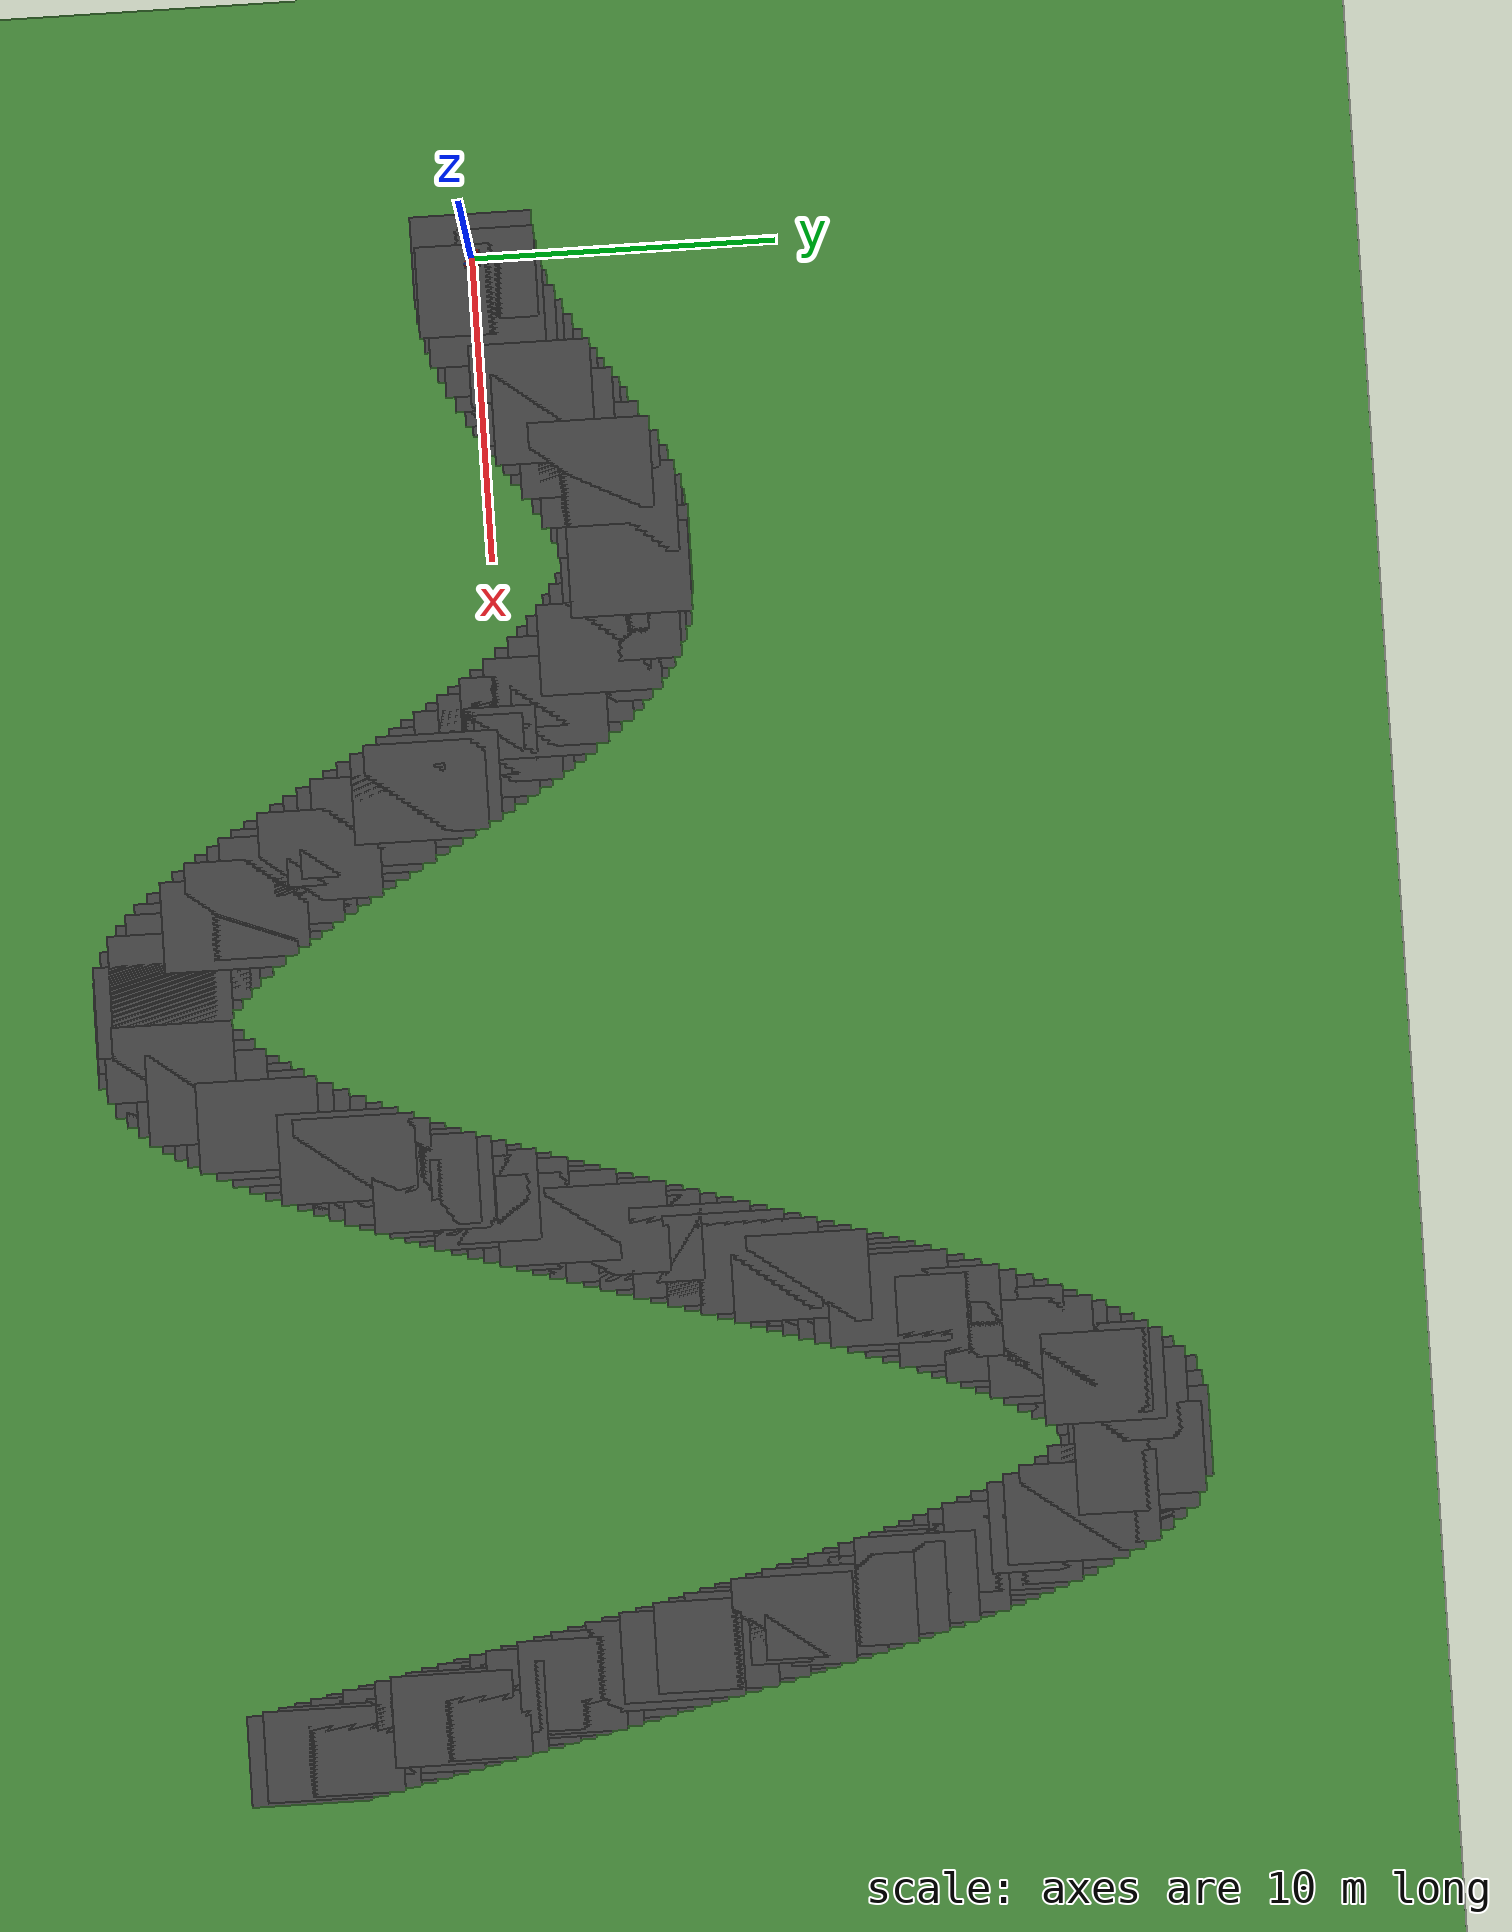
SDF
<sdf version="1.7">
 <world name="default">
  <scene>
   <sky><clouds><speed>12</speed></clouds></sky>
   <grid>0</grid>
   <ambient>0.4 0.4 0.4 1</ambient>
   <background>0.7 0.7 0.7 1</background>
   <shadows>0</shadows>
  </scene>
  <model name="grass_floor">
   <static>1</static>
   <link name="link">
    <collision name="collision">
     <geometry><plane><normal>0 0 1</normal><size>500 700</size></plane></geometry>
     <surface><friction><ode><mu>100</mu><mu2>50</mu2></ode></friction></surface>
    </collision>
    <visual name="visual">
     <cast_shadows>0</cast_shadows>
     <geometry><plane><normal>0 0 1</normal><size>500 700</size></plane></geometry>
     <material>
      <script><uri>file://media/materials/scripts/gazebo.material</uri><name>Gazebo/Grass</name></script>
     </material>
    </visual>
   </link>
   <pose>200 250 0 0 -0 0</pose>
  </model>
  <light name="sun" type="directional">
   <pose>0 0 10 0 -0 0</pose>
   <diffuse>0.8 0.8 0.8 1</diffuse>
   <specular>0.2 0.2 0.2 1</specular>
   <attenuation>
    <range>1000</range>
    <constant>0.9</constant>
    <linear>0.01</linear>
    <quadratic>0.001</quadratic>
   </attenuation>
   <direction>-0.5 0.1 -0.9</direction>
   <spot><inner_angle>0</inner_angle><outer_angle>0</outer_angle><falloff>0</falloff></spot>
  </light>
  <physics name="default_physics" default="0" type="ode">
   <ode>
    <solver>
     <type>quick</type>
     <iters>10</iters>
     <sor>1.3</sor>
     <use_dynamic_moi_rescaling>0</use_dynamic_moi_rescaling>
    </solver>
    <constraints>
     <cfm>0</cfm>
     <erp>0.2</erp>
     <contact_max_correcting_vel>100</contact_max_correcting_vel>
     <contact_surface_layer>0.001</contact_surface_layer>
    </constraints>
   </ode>
   <max_step_size>0.001</max_step_size>
   <real_time_factor>1</real_time_factor>
   <real_time_update_rate>1000</real_time_update_rate>
   <gravity>0 0 -9.8066</gravity>
   <magnetic_field>6.0e-6 2.3e-5 -4.2e-5</magnetic_field>
  </physics>
  <gravity>0 0 -9.8</gravity>
  <magnetic_field>6e-06 2.3e-05 -4.2e-05</magnetic_field>
  <atmosphere type="adiabatic"/>
  <spherical_coordinates>
   <surface_model>EARTH_WGS84</surface_model>
   <latitude_deg>0</latitude_deg>
   <longitude_deg>0</longitude_deg>
   <elevation>0</elevation>
   <heading_deg>0</heading_deg>
  </spherical_coordinates>
  <model name="steer_bot">
   <link name="base_link">
    <inertial>
     <pose>0.00098 0.00098 0.001961 0 -0 0</pose>
     <mass>5.1</mass>
     <inertia>
      <ixx>0.042913</ixx>
      <ixy>-0.000245098</ixy>
      <ixz>-0.000490196</ixz>
      <iyy>0.10958</iyy>
      <iyz>-0.000490196</iyz>
      <izz>0.142157</izz>
     </inertia>
    </inertial>
    <collision name="base_link_collision"><geometry><box><size>0.5 0.3 0.1</size></box></geometry></collision>
    <collision name="base_link_fixed_joint_lump__imu_box_collision_1">
     <pose>0 0 0.05 0 -0 0</pose>
     <geometry><box><size>0.05 0.05 0.05</size></box></geometry>
    </collision>
    <visual name="base_link_visual">
     <geometry><box><size>0.5 0.3 0.1</size></box></geometry>
     <material>
      <script><name>Gazebo/Green</name><uri>file://media/materials/scripts/gazebo.material</uri></script>
     </material>
    </visual>
    <visual name="base_link_fixed_joint_lump__imu_box_visual_1">
     <pose>0 0 0.05 0 -0 0</pose>
     <geometry><box><size>0.05 0.05 0.05</size></box></geometry>
     <material>
      <script><name>Gazebo/White</name><uri>file://media/materials/scripts/gazebo.material</uri></script>
     </material>
    </visual>
    <sensor name="imu_sensor" type="imu">
     <always_on>1</always_on>
     <update_rate>100</update_rate>
     <visualize>1</visualize>
     <topic>__default_topic__</topic>
     <plugin name="imu_plugin" filename="libgazebo_ros_imu_sensor.so">
      <topicName>imu</topicName>
      <bodyName>imu_link</bodyName>
      <updateRateHZ>10.0</updateRateHZ>
      <gaussianNoise>2.89e-08</gaussianNoise>
      <xyzOffset>0 0 0</xyzOffset>
      <rpyOffset>0 0 0</rpyOffset>
      <frameName>imu_link</frameName>
      <inertialOrientationAsReference>0</inertialOrientationAsReference>
      <robotNamespace>/steer_bot/</robotNamespace>
     </plugin>
     <pose>0 0 0.05 0 -0 0</pose>
    </sensor>
   </link>
   <joint name="front_left_steer_joint" type="revolute">
    <pose relative_to="base_link">0.2 0.2 0.12 0 -0 0</pose>
    <parent>base_link</parent>
    <child>front_left_steer_link</child>
    <axis>
     <xyz>0 0 1</xyz>
     <limit><lower>-0.785398</lower><upper>0.785398</upper><effort>10</effort><velocity>5</velocity></limit>
     <dynamics><spring_reference>0</spring_reference><spring_stiffness>0</spring_stiffness></dynamics>
    </axis>
   </joint>
   <link name="front_left_steer_link">
    <pose relative_to="front_left_steer_joint">0 0 0 0 -0 0</pose>
    <inertial>
     <mass>1</mass>
     <inertia>
      <ixx>0.000658333</ixx>
      <ixy>0</ixy>
      <ixz>0</ixz>
      <iyy>0.000658333</iyy>
      <iyz>0</iyz>
      <izz>0.00125</izz>
     </inertia>
    </inertial>
    <collision name="front_left_steer_link_collision">
     <geometry><cylinder><length>0.02</length><radius>0.05</radius></cylinder></geometry>
    </collision>
    <visual name="front_left_steer_link_visual">
     <geometry><cylinder><length>0.02</length><radius>0.05</radius></cylinder></geometry>
     <material>
      <script><name>Gazebo/Blue</name><uri>file://media/materials/scripts/gazebo.material</uri></script>
     </material>
    </visual>
   </link>
   <joint name="front_left_wheel_joint" type="revolute">
    <pose relative_to="front_left_steer_link">0 0 -0.12 -1.5708 0 0</pose>
    <parent>front_left_steer_link</parent>
    <child>front_left_wheel_link</child>
    <axis>
     <xyz>0 0 1</xyz>
     <limit><lower>-1e+16</lower><upper>1e+16</upper></limit>
     <dynamics><spring_reference>0</spring_reference><spring_stiffness>0</spring_stiffness></dynamics>
    </axis>
   </joint>
   <link name="front_left_wheel_link">
    <pose relative_to="front_left_wheel_joint">0 0 0 0 -0 0</pose>
    <inertial>
     <mass>1</mass>
     <inertia>
      <ixx>0.00303333</ixx>
      <ixy>0</ixy>
      <ixz>0</ixz>
      <iyy>0.00303333</iyy>
      <iyz>0</iyz>
      <izz>0.005</izz>
     </inertia>
    </inertial>
    <collision name="front_left_wheel_link_collision">
     <geometry><cylinder><length>0.08</length><radius>0.1</radius></cylinder></geometry>
    </collision>
    <visual name="front_left_wheel_link_visual">
     <geometry><cylinder><length>0.08</length><radius>0.1</radius></cylinder></geometry>
     <material>
      <script><name>Gazebo/Red</name><uri>file://media/materials/scripts/gazebo.material</uri></script>
     </material>
    </visual>
   </link>
   <joint name="front_right_steer_joint" type="revolute">
    <pose relative_to="base_link">0.2 -0.2 0.12 0 -0 0</pose>
    <parent>base_link</parent>
    <child>front_right_steer_link</child>
    <axis>
     <xyz>0 0 1</xyz>
     <limit><lower>-0.785398</lower><upper>0.785398</upper><effort>10</effort><velocity>5</velocity></limit>
     <dynamics><spring_reference>0</spring_reference><spring_stiffness>0</spring_stiffness></dynamics>
    </axis>
   </joint>
   <link name="front_right_steer_link">
    <pose relative_to="front_right_steer_joint">0 0 0 0 -0 0</pose>
    <inertial>
     <mass>1</mass>
     <inertia>
      <ixx>0.000658333</ixx>
      <ixy>0</ixy>
      <ixz>0</ixz>
      <iyy>0.000658333</iyy>
      <iyz>0</iyz>
      <izz>0.00125</izz>
     </inertia>
    </inertial>
    <collision name="front_right_steer_link_collision">
     <geometry><cylinder><length>0.02</length><radius>0.05</radius></cylinder></geometry>
    </collision>
    <visual name="front_right_steer_link_visual">
     <geometry><cylinder><length>0.02</length><radius>0.05</radius></cylinder></geometry>
     <material>
      <script><name>Gazebo/Blue</name><uri>file://media/materials/scripts/gazebo.material</uri></script>
     </material>
    </visual>
   </link>
   <joint name="front_right_wheel_joint" type="revolute">
    <pose relative_to="front_right_steer_link">0 0 -0.12 -1.5708 0 0</pose>
    <parent>front_right_steer_link</parent>
    <child>front_right_wheel_link</child>
    <axis>
     <xyz>0 0 1</xyz>
     <limit><lower>-1e+16</lower><upper>1e+16</upper></limit>
     <dynamics><spring_reference>0</spring_reference><spring_stiffness>0</spring_stiffness></dynamics>
    </axis>
   </joint>
   <link name="front_right_wheel_link">
    <pose relative_to="front_right_wheel_joint">0 0 0 0 -0 0</pose>
    <inertial>
     <mass>1</mass>
     <inertia>
      <ixx>0.00303333</ixx>
      <ixy>0</ixy>
      <ixz>0</ixz>
      <iyy>0.00303333</iyy>
      <iyz>0</iyz>
      <izz>0.005</izz>
     </inertia>
    </inertial>
    <collision name="front_right_wheel_link_collision">
     <geometry><cylinder><length>0.08</length><radius>0.1</radius></cylinder></geometry>
    </collision>
    <visual name="front_right_wheel_link_visual">
     <geometry><cylinder><length>0.08</length><radius>0.1</radius></cylinder></geometry>
     <material>
      <script><name>Gazebo/Red</name><uri>file://media/materials/scripts/gazebo.material</uri></script>
     </material>
    </visual>
   </link>
   <joint name="front_steer_joint" type="revolute">
    <pose relative_to="base_link">0.2 0 0.12 0 -0 0</pose>
    <parent>base_link</parent>
    <child>front_steer_link</child>
    <axis>
     <xyz>0 0 1</xyz>
     <limit><lower>-3.14159</lower><upper>3.14159</upper><effort>10</effort><velocity>5</velocity></limit>
     <dynamics><spring_reference>0</spring_reference><spring_stiffness>0</spring_stiffness></dynamics>
    </axis>
   </joint>
   <link name="front_steer_link">
    <pose relative_to="front_steer_joint">0 0 0 0 -0 0</pose>
    <inertial>
     <mass>1</mass>
     <inertia>
      <ixx>0.000658333</ixx>
      <ixy>0</ixy>
      <ixz>0</ixz>
      <iyy>0.000658333</iyy>
      <iyz>0</iyz>
      <izz>0.00125</izz>
     </inertia>
    </inertial>
    <collision name="front_steer_link_collision">
     <geometry><cylinder><length>0.02</length><radius>0.05</radius></cylinder></geometry>
    </collision>
    <visual name="front_steer_link_visual">
     <geometry><cylinder><length>0.02</length><radius>0.05</radius></cylinder></geometry>
     <material>
      <script><name>Gazebo/Yellow</name><uri>file://media/materials/scripts/gazebo.material</uri></script>
     </material>
    </visual>
   </link>
   <joint name="rear_left_wheel_joint" type="revolute">
    <pose relative_to="base_link">-0.2 0.2 0 -1.5708 0 0</pose>
    <parent>base_link</parent>
    <child>rear_left_wheel_link</child>
    <axis>
     <xyz>0 0 1</xyz>
     <limit><lower>-1e+16</lower><upper>1e+16</upper></limit>
     <dynamics><spring_reference>0</spring_reference><spring_stiffness>0</spring_stiffness></dynamics>
    </axis>
   </joint>
   <link name="rear_left_wheel_link">
    <pose relative_to="rear_left_wheel_joint">0 0 0 0 -0 0</pose>
    <inertial>
     <mass>1</mass>
     <inertia>
      <ixx>0.00303333</ixx>
      <ixy>0</ixy>
      <ixz>0</ixz>
      <iyy>0.00303333</iyy>
      <iyz>0</iyz>
      <izz>0.005</izz>
     </inertia>
    </inertial>
    <collision name="rear_left_wheel_link_collision">
     <geometry><cylinder><length>0.08</length><radius>0.1</radius></cylinder></geometry>
    </collision>
    <visual name="rear_left_wheel_link_visual">
     <geometry><cylinder><length>0.08</length><radius>0.1</radius></cylinder></geometry>
     <material>
      <script><name>Gazebo/Red</name><uri>file://media/materials/scripts/gazebo.material</uri></script>
     </material>
    </visual>
   </link>
   <joint name="rear_right_wheel_joint" type="revolute">
    <pose relative_to="base_link">-0.2 -0.2 0 -1.5708 0 0</pose>
    <parent>base_link</parent>
    <child>rear_right_wheel_link</child>
    <axis>
     <xyz>0 0 1</xyz>
     <limit><lower>-1e+16</lower><upper>1e+16</upper></limit>
     <dynamics><spring_reference>0</spring_reference><spring_stiffness>0</spring_stiffness></dynamics>
    </axis>
   </joint>
   <link name="rear_right_wheel_link">
    <pose relative_to="rear_right_wheel_joint">0 0 0 0 -0 0</pose>
    <inertial>
     <mass>1</mass>
     <inertia>
      <ixx>0.00303333</ixx>
      <ixy>0</ixy>
      <ixz>0</ixz>
      <iyy>0.00303333</iyy>
      <iyz>0</iyz>
      <izz>0.005</izz>
     </inertia>
    </inertial>
    <collision name="rear_right_wheel_link_collision">
     <geometry><cylinder><length>0.08</length><radius>0.1</radius></cylinder></geometry>
    </collision>
    <visual name="rear_right_wheel_link_visual">
     <geometry><cylinder><length>0.08</length><radius>0.1</radius></cylinder></geometry>
     <material>
      <script><name>Gazebo/Red</name><uri>file://media/materials/scripts/gazebo.material</uri></script>
     </material>
    </visual>
   </link>
   <joint name="rear_wheel_joint" type="revolute">
    <pose relative_to="base_link">-0.2 0 0 -1.5708 0 0</pose>
    <parent>base_link</parent>
    <child>rear_wheel_link</child>
    <axis>
     <xyz>0 0 1</xyz>
     <limit><lower>-1e+16</lower><upper>1e+16</upper></limit>
     <dynamics><spring_reference>0</spring_reference><spring_stiffness>0</spring_stiffness></dynamics>
    </axis>
   </joint>
   <link name="rear_wheel_link">
    <pose relative_to="rear_wheel_joint">0 0 0 0 -0 0</pose>
    <inertial>
     <mass>0.03125</mass>
     <inertia>
      <ixx>9.04948e-06</ixx>
      <ixy>0</ixy>
      <ixz>0</ixz>
      <iyy>9.04948e-06</iyy>
      <iyz>0</iyz>
      <izz>9.76563e-06</izz>
     </inertia>
    </inertial>
    <collision name="rear_wheel_link_collision">
     <geometry><cylinder><length>0.04</length><radius>0.025</radius></cylinder></geometry>
    </collision>
    <visual name="rear_wheel_link_visual">
     <geometry><cylinder><length>0.04</length><radius>0.025</radius></cylinder></geometry>
     <material>
      <script><name>Gazebo/Yellow</name><uri>file://media/materials/scripts/gazebo.material</uri></script>
     </material>
    </visual>
   </link>
   <static>0</static>
   <plugin name="gazebo_ros_control" filename="libgazebo_ros_control.so">
    <robotNamespace>/steer_bot</robotNamespace>
    <robotSimType>steer_bot_hardware_gazebo/SteerBotHardwareGazebo</robotSimType>
    <legacyModeNS>0</legacyModeNS>
   </plugin>
   <plugin name="p3d_base_controller" filename="libgazebo_ros_p3d.so">
    <alwaysOn>1</alwaysOn>
    <updateRate>50.0</updateRate>
    <bodyName>base_link</bodyName>
    <topicName>pose_ground_truth</topicName>
    <gaussianNoise>0.00</gaussianNoise>
    <frameName>world</frameName>
    <xyzOffsets>0 0 0</xyzOffsets>
    <rpyOffsets>0 0 0</rpyOffsets>
    <robotNamespace>/steer_bot/</robotNamespace>
   </plugin>
   <pose>-0.002082 -0.017108 0.104996 0 6e-06 -0.057589</pose>
  </model>
  <model name="roadSegment_0_0">
   <static>1</static>
   <link name="link">
    <collision name="collision"><geometry><box><size>3 4 0.01</size></box></geometry></collision>
    <visual name="visual">
     <cast_shadows>0</cast_shadows>
     <geometry><box><size>3 4 0.01</size></box></geometry>
     <material>
      <script>
       <uri>model://asphalt_plane/materials/scripts</uri>
       <uri>model://asphalt_plane/materials/textures</uri>
       <name>vrc/asphalt</name>
      </script>
     </material>
    </visual>
   </link>
  </model>
  <model name="roadSegment_0_1">
   <static>1</static>
   <link name="link">
    <collision name="collision"><geometry><box><size>3 4 0.01</size></box></geometry></collision>
    <visual name="visual">
     <cast_shadows>0</cast_shadows>
     <geometry><box><size>3 4 0.01</size></box></geometry>
     <material>
      <script>
       <uri>model://asphalt_plane/materials/scripts</uri>
       <uri>model://asphalt_plane/materials/textures</uri>
       <name>vrc/asphalt</name>
      </script>
     </material>
    </visual>
   </link>
   <pose>0.5 0.049667 0 0 -0 0</pose>
  </model>
  <model name="roadSegment_1_0">
   <static>1</static>
   <link name="link">
    <collision name="collision"><geometry><box><size>3 4 0.01</size></box></geometry></collision>
    <visual name="visual">
     <cast_shadows>0</cast_shadows>
     <geometry><box><size>3 4 0.01</size></box></geometry>
     <material>
      <script>
       <uri>model://asphalt_plane/materials/scripts</uri>
       <uri>model://asphalt_plane/materials/textures</uri>
       <name>vrc/asphalt</name>
      </script>
     </material>
    </visual>
   </link>
   <pose>1 0.099335 0 0 -0 0</pose>
  </model>
  <model name="roadSegment_1_1">
   <static>1</static>
   <link name="link">
    <collision name="collision"><geometry><box><size>3 4 0.01</size></box></geometry></collision>
    <visual name="visual">
     <cast_shadows>0</cast_shadows>
     <geometry><box><size>3 4 0.01</size></box></geometry>
     <material>
      <script>
       <uri>model://asphalt_plane/materials/scripts</uri>
       <uri>model://asphalt_plane/materials/textures</uri>
       <name>vrc/asphalt</name>
      </script>
     </material>
    </visual>
   </link>
   <pose>1.5 0.244377 0 0 -0 0</pose>
  </model>
  <model name="roadSegment_2_0">
   <static>1</static>
   <link name="link">
    <collision name="collision"><geometry><box><size>3 4 0.01</size></box></geometry></collision>
    <visual name="visual">
     <cast_shadows>0</cast_shadows>
     <geometry><box><size>3 4 0.01</size></box></geometry>
     <material>
      <script>
       <uri>model://asphalt_plane/materials/scripts</uri>
       <uri>model://asphalt_plane/materials/textures</uri>
       <name>vrc/asphalt</name>
      </script>
     </material>
    </visual>
   </link>
   <pose>2 0.389418 0 0 -0 0</pose>
  </model>
  <model name="roadSegment_2_1">
   <static>1</static>
   <link name="link">
    <collision name="collision"><geometry><box><size>3 4 0.01</size></box></geometry></collision>
    <visual name="visual">
     <cast_shadows>0</cast_shadows>
     <geometry><box><size>3 4 0.01</size></box></geometry>
     <material>
      <script>
       <uri>model://asphalt_plane/materials/scripts</uri>
       <uri>model://asphalt_plane/materials/textures</uri>
       <name>vrc/asphalt</name>
      </script>
     </material>
    </visual>
   </link>
   <pose>2.5 0.618191 0 0 -0 0</pose>
  </model>
  <model name="roadSegment_3_0">
   <static>1</static>
   <link name="link">
    <collision name="collision"><geometry><box><size>3 4 0.01</size></box></geometry></collision>
    <visual name="visual">
     <cast_shadows>0</cast_shadows>
     <geometry><box><size>3 4 0.01</size></box></geometry>
     <material>
      <script>
       <uri>model://asphalt_plane/materials/scripts</uri>
       <uri>model://asphalt_plane/materials/textures</uri>
       <name>vrc/asphalt</name>
      </script>
     </material>
    </visual>
   </link>
   <pose>3 0.846964 0 0 -0 0</pose>
  </model>
  <model name="roadSegment_3_1">
   <static>1</static>
   <link name="link">
    <collision name="collision"><geometry><box><size>3 4 0.01</size></box></geometry></collision>
    <visual name="visual">
     <cast_shadows>0</cast_shadows>
     <geometry><box><size>3 4 0.01</size></box></geometry>
     <material>
      <script>
       <uri>model://asphalt_plane/materials/scripts</uri>
       <uri>model://asphalt_plane/materials/textures</uri>
       <name>vrc/asphalt</name>
      </script>
     </material>
    </visual>
   </link>
   <pose>3.5 1.14084 0 0 -0 0</pose>
  </model>
  <model name="roadSegment_4_0">
   <static>1</static>
   <link name="link">
    <collision name="collision"><geometry><box><size>3 4 0.01</size></box></geometry></collision>
    <visual name="visual">
     <cast_shadows>0</cast_shadows>
     <geometry><box><size>3 4 0.01</size></box></geometry>
     <material>
      <script>
       <uri>model://asphalt_plane/materials/scripts</uri>
       <uri>model://asphalt_plane/materials/textures</uri>
       <name>vrc/asphalt</name>
      </script>
     </material>
    </visual>
   </link>
   <pose>4 1.43471 0 0 -0 0</pose>
  </model>
  <model name="roadSegment_4_1">
   <static>1</static>
   <link name="link">
    <collision name="collision"><geometry><box><size>3 4 0.01</size></box></geometry></collision>
    <visual name="visual">
     <cast_shadows>0</cast_shadows>
     <geometry><box><size>3 4 0.01</size></box></geometry>
     <material>
      <script>
       <uri>model://asphalt_plane/materials/scripts</uri>
       <uri>model://asphalt_plane/materials/textures</uri>
       <name>vrc/asphalt</name>
      </script>
     </material>
    </visual>
   </link>
   <pose>4.33333 1.6577 0 0 -0 0</pose>
  </model>
  <model name="roadSegment_4_2">
   <static>1</static>
   <link name="link">
    <collision name="collision"><geometry><box><size>3 4 0.01</size></box></geometry></collision>
    <visual name="visual">
     <cast_shadows>0</cast_shadows>
     <geometry><box><size>3 4 0.01</size></box></geometry>
     <material>
      <script>
       <uri>model://asphalt_plane/materials/scripts</uri>
       <uri>model://asphalt_plane/materials/textures</uri>
       <name>vrc/asphalt</name>
      </script>
     </material>
    </visual>
   </link>
   <pose>4.66667 1.88069 0 0 -0 0</pose>
  </model>
  <model name="roadSegment_5_0">
   <static>1</static>
   <link name="link">
    <collision name="collision"><geometry><box><size>3 4 0.01</size></box></geometry></collision>
    <visual name="visual">
     <cast_shadows>0</cast_shadows>
     <geometry><box><size>3 4 0.01</size></box></geometry>
     <material>
      <script>
       <uri>model://asphalt_plane/materials/scripts</uri>
       <uri>model://asphalt_plane/materials/textures</uri>
       <name>vrc/asphalt</name>
      </script>
     </material>
    </visual>
   </link>
   <pose>5 2.10368 0 0 -0 0</pose>
  </model>
  <model name="roadSegment_5_1">
   <static>1</static>
   <link name="link">
    <collision name="collision"><geometry><box><size>3 4 0.01</size></box></geometry></collision>
    <visual name="visual">
     <cast_shadows>0</cast_shadows>
     <geometry><box><size>3 4 0.01</size></box></geometry>
     <material>
      <script>
       <uri>model://asphalt_plane/materials/scripts</uri>
       <uri>model://asphalt_plane/materials/textures</uri>
       <name>vrc/asphalt</name>
      </script>
     </material>
    </visual>
   </link>
   <pose>5.33333 2.33449 0 0 -0 0</pose>
  </model>
  <model name="roadSegment_5_2">
   <static>1</static>
   <link name="link">
    <collision name="collision"><geometry><box><size>3 4 0.01</size></box></geometry></collision>
    <visual name="visual">
     <cast_shadows>0</cast_shadows>
     <geometry><box><size>3 4 0.01</size></box></geometry>
     <material>
      <script>
       <uri>model://asphalt_plane/materials/scripts</uri>
       <uri>model://asphalt_plane/materials/textures</uri>
       <name>vrc/asphalt</name>
      </script>
     </material>
    </visual>
   </link>
   <pose>5.66667 2.5653 0 0 -0 0</pose>
  </model>
  <model name="roadSegment_6_0">
   <static>1</static>
   <link name="link">
    <collision name="collision"><geometry><box><size>3 4 0.01</size></box></geometry></collision>
    <visual name="visual">
     <cast_shadows>0</cast_shadows>
     <geometry><box><size>3 4 0.01</size></box></geometry>
     <material>
      <script>
       <uri>model://asphalt_plane/materials/scripts</uri>
       <uri>model://asphalt_plane/materials/textures</uri>
       <name>vrc/asphalt</name>
      </script>
     </material>
    </visual>
   </link>
   <pose>6 2.79612 0 0 -0 0</pose>
  </model>
  <model name="roadSegment_6_1">
   <static>1</static>
   <link name="link">
    <collision name="collision"><geometry><box><size>3 4 0.01</size></box></geometry></collision>
    <visual name="visual">
     <cast_shadows>0</cast_shadows>
     <geometry><box><size>3 4 0.01</size></box></geometry>
     <material>
      <script>
       <uri>model://asphalt_plane/materials/scripts</uri>
       <uri>model://asphalt_plane/materials/textures</uri>
       <name>vrc/asphalt</name>
      </script>
     </material>
    </visual>
   </link>
   <pose>6.5 3.1226 0 0 -0 0</pose>
  </model>
  <model name="roadSegment_7_0">
   <static>1</static>
   <link name="link">
    <collision name="collision"><geometry><box><size>3 4 0.01</size></box></geometry></collision>
    <visual name="visual">
     <cast_shadows>0</cast_shadows>
     <geometry><box><size>3 4 0.01</size></box></geometry>
     <material>
      <script>
       <uri>model://asphalt_plane/materials/scripts</uri>
       <uri>model://asphalt_plane/materials/textures</uri>
       <name>vrc/asphalt</name>
      </script>
     </material>
    </visual>
   </link>
   <pose>7 3.44907 0 0 -0 0</pose>
  </model>
  <model name="roadSegment_7_1">
   <static>1</static>
   <link name="link">
    <collision name="collision"><geometry><box><size>3 4 0.01</size></box></geometry></collision>
    <visual name="visual">
     <cast_shadows>0</cast_shadows>
     <geometry><box><size>3 4 0.01</size></box></geometry>
     <material>
      <script>
       <uri>model://asphalt_plane/materials/scripts</uri>
       <uri>model://asphalt_plane/materials/textures</uri>
       <name>vrc/asphalt</name>
      </script>
     </material>
    </visual>
   </link>
   <pose>7.5 3.72368 0 0 -0 0</pose>
  </model>
  <model name="roadSegment_8_0">
   <static>1</static>
   <link name="link">
    <collision name="collision"><geometry><box><size>3 4 0.01</size></box></geometry></collision>
    <visual name="visual">
     <cast_shadows>0</cast_shadows>
     <geometry><box><size>3 4 0.01</size></box></geometry>
     <material>
      <script>
       <uri>model://asphalt_plane/materials/scripts</uri>
       <uri>model://asphalt_plane/materials/textures</uri>
       <name>vrc/asphalt</name>
      </script>
     </material>
    </visual>
   </link>
   <pose>8 3.99829 0 0 -0 0</pose>
  </model>
  <model name="roadSegment_8_1">
   <static>1</static>
   <link name="link">
    <collision name="collision"><geometry><box><size>3 4 0.01</size></box></geometry></collision>
    <visual name="visual">
     <cast_shadows>0</cast_shadows>
     <geometry><box><size>3 4 0.01</size></box></geometry>
     <material>
      <script>
       <uri>model://asphalt_plane/materials/scripts</uri>
       <uri>model://asphalt_plane/materials/textures</uri>
       <name>vrc/asphalt</name>
      </script>
     </material>
    </visual>
   </link>
   <pose>8.5 4.1903 0 0 -0 0</pose>
  </model>
  <model name="roadSegment_9_0">
   <static>1</static>
   <link name="link">
    <collision name="collision"><geometry><box><size>3 4 0.01</size></box></geometry></collision>
    <visual name="visual">
     <cast_shadows>0</cast_shadows>
     <geometry><box><size>3 4 0.01</size></box></geometry>
     <material>
      <script>
       <uri>model://asphalt_plane/materials/scripts</uri>
       <uri>model://asphalt_plane/materials/textures</uri>
       <name>vrc/asphalt</name>
      </script>
     </material>
    </visual>
   </link>
   <pose>9 4.38231 0 0 -0 0</pose>
  </model>
  <model name="roadSegment_9_1">
   <static>1</static>
   <link name="link">
    <collision name="collision"><geometry><box><size>3 4 0.01</size></box></geometry></collision>
    <visual name="visual">
     <cast_shadows>0</cast_shadows>
     <geometry><box><size>3 4 0.01</size></box></geometry>
     <material>
      <script>
       <uri>model://asphalt_plane/materials/scripts</uri>
       <uri>model://asphalt_plane/materials/textures</uri>
       <name>vrc/asphalt</name>
      </script>
     </material>
    </visual>
   </link>
   <pose>9.5 4.4644 0 0 -0 0</pose>
  </model>
  <model name="roadSegment_10_0">
   <static>1</static>
   <link name="link">
    <collision name="collision"><geometry><box><size>3 4 0.01</size></box></geometry></collision>
    <visual name="visual">
     <cast_shadows>0</cast_shadows>
     <geometry><box><size>3 4 0.01</size></box></geometry>
     <material>
      <script>
       <uri>model://asphalt_plane/materials/scripts</uri>
       <uri>model://asphalt_plane/materials/textures</uri>
       <name>vrc/asphalt</name>
      </script>
     </material>
    </visual>
   </link>
   <pose>10 4.54649 0 0 -0 0</pose>
  </model>
  <model name="roadSegment_10_1">
   <static>1</static>
   <link name="link">
    <collision name="collision"><geometry><box><size>3 4 0.01</size></box></geometry></collision>
    <visual name="visual">
     <cast_shadows>0</cast_shadows>
     <geometry><box><size>3 4 0.01</size></box></geometry>
     <material>
      <script>
       <uri>model://asphalt_plane/materials/scripts</uri>
       <uri>model://asphalt_plane/materials/textures</uri>
       <name>vrc/asphalt</name>
      </script>
     </material>
    </visual>
   </link>
   <pose>10.5 4.49661 0 0 -0 0</pose>
  </model>
  <model name="roadSegment_11_0">
   <static>1</static>
   <link name="link">
    <collision name="collision"><geometry><box><size>3 4 0.01</size></box></geometry></collision>
    <visual name="visual">
     <cast_shadows>0</cast_shadows>
     <geometry><box><size>3 4 0.01</size></box></geometry>
     <material>
      <script>
       <uri>model://asphalt_plane/materials/scripts</uri>
       <uri>model://asphalt_plane/materials/textures</uri>
       <name>vrc/asphalt</name>
      </script>
     </material>
    </visual>
   </link>
   <pose>11 4.44673 0 0 -0 0</pose>
  </model>
  <model name="roadSegment_11_1">
   <static>1</static>
   <link name="link">
    <collision name="collision"><geometry><box><size>3 4 0.01</size></box></geometry></collision>
    <visual name="visual">
     <cast_shadows>0</cast_shadows>
     <geometry><box><size>3 4 0.01</size></box></geometry>
     <material>
      <script>
       <uri>model://asphalt_plane/materials/scripts</uri>
       <uri>model://asphalt_plane/materials/textures</uri>
       <name>vrc/asphalt</name>
      </script>
     </material>
    </visual>
   </link>
   <pose>11.5 4.24975 0 0 -0 0</pose>
  </model>
  <model name="roadSegment_12_0">
   <static>1</static>
   <link name="link">
    <collision name="collision"><geometry><box><size>3 4 0.01</size></box></geometry></collision>
    <visual name="visual">
     <cast_shadows>0</cast_shadows>
     <geometry><box><size>3 4 0.01</size></box></geometry>
     <material>
      <script>
       <uri>model://asphalt_plane/materials/scripts</uri>
       <uri>model://asphalt_plane/materials/textures</uri>
       <name>vrc/asphalt</name>
      </script>
     </material>
    </visual>
   </link>
   <pose>12 4.05278 0 0 -0 0</pose>
  </model>
  <model name="roadSegment_12_1">
   <static>1</static>
   <link name="link">
    <collision name="collision"><geometry><box><size>3 4 0.01</size></box></geometry></collision>
    <visual name="visual">
     <cast_shadows>0</cast_shadows>
     <geometry><box><size>3 4 0.01</size></box></geometry>
     <material>
      <script>
       <uri>model://asphalt_plane/materials/scripts</uri>
       <uri>model://asphalt_plane/materials/textures</uri>
       <name>vrc/asphalt</name>
      </script>
     </material>
    </visual>
   </link>
   <pose>12.3333 3.81877 0 0 -0 0</pose>
  </model>
  <model name="roadSegment_12_2">
   <static>1</static>
   <link name="link">
    <collision name="collision"><geometry><box><size>3 4 0.01</size></box></geometry></collision>
    <visual name="visual">
     <cast_shadows>0</cast_shadows>
     <geometry><box><size>3 4 0.01</size></box></geometry>
     <material>
      <script>
       <uri>model://asphalt_plane/materials/scripts</uri>
       <uri>model://asphalt_plane/materials/textures</uri>
       <name>vrc/asphalt</name>
      </script>
     </material>
    </visual>
   </link>
   <pose>12.6667 3.58477 0 0 -0 0</pose>
  </model>
  <model name="roadSegment_13_0">
   <static>1</static>
   <link name="link">
    <collision name="collision"><geometry><box><size>3 4 0.01</size></box></geometry></collision>
    <visual name="visual">
     <cast_shadows>0</cast_shadows>
     <geometry><box><size>3 4 0.01</size></box></geometry>
     <material>
      <script>
       <uri>model://asphalt_plane/materials/scripts</uri>
       <uri>model://asphalt_plane/materials/textures</uri>
       <name>vrc/asphalt</name>
      </script>
     </material>
    </visual>
   </link>
   <pose>13 3.35076 0 0 -0 0</pose>
  </model>
  <model name="roadSegment_13_1">
   <static>1</static>
   <link name="link">
    <collision name="collision"><geometry><box><size>3 4 0.01</size></box></geometry></collision>
    <visual name="visual">
     <cast_shadows>0</cast_shadows>
     <geometry><box><size>3 4 0.01</size></box></geometry>
     <material>
      <script>
       <uri>model://asphalt_plane/materials/scripts</uri>
       <uri>model://asphalt_plane/materials/textures</uri>
       <name>vrc/asphalt</name>
      </script>
     </material>
    </visual>
   </link>
   <pose>13.3333 3.01548 0 0 -0 0</pose>
  </model>
  <model name="roadSegment_13_2">
   <static>1</static>
   <link name="link">
    <collision name="collision"><geometry><box><size>3 4 0.01</size></box></geometry></collision>
    <visual name="visual">
     <cast_shadows>0</cast_shadows>
     <geometry><box><size>3 4 0.01</size></box></geometry>
     <material>
      <script>
       <uri>model://asphalt_plane/materials/scripts</uri>
       <uri>model://asphalt_plane/materials/textures</uri>
       <name>vrc/asphalt</name>
      </script>
     </material>
    </visual>
   </link>
   <pose>13.6667 2.6802 0 0 -0 0</pose>
  </model>
  <model name="roadSegment_14_0">
   <static>1</static>
   <link name="link">
    <collision name="collision"><geometry><box><size>3 4 0.01</size></box></geometry></collision>
    <visual name="visual">
     <cast_shadows>0</cast_shadows>
     <geometry><box><size>3 4 0.01</size></box></geometry>
     <material>
      <script>
       <uri>model://asphalt_plane/materials/scripts</uri>
       <uri>model://asphalt_plane/materials/textures</uri>
       <name>vrc/asphalt</name>
      </script>
     </material>
    </visual>
   </link>
   <pose>14 2.34492 0 0 -0 0</pose>
  </model>
  <model name="roadSegment_14_1">
   <static>1</static>
   <link name="link">
    <collision name="collision"><geometry><box><size>3 4 0.01</size></box></geometry></collision>
    <visual name="visual">
     <cast_shadows>0</cast_shadows>
     <geometry><box><size>3 4 0.01</size></box></geometry>
     <material>
      <script>
       <uri>model://asphalt_plane/materials/scripts</uri>
       <uri>model://asphalt_plane/materials/textures</uri>
       <name>vrc/asphalt</name>
      </script>
     </material>
    </visual>
   </link>
   <pose>14.3333 1.91608 0 0 -0 0</pose>
  </model>
  <model name="roadSegment_14_2">
   <static>1</static>
   <link name="link">
    <collision name="collision"><geometry><box><size>3 4 0.01</size></box></geometry></collision>
    <visual name="visual">
     <cast_shadows>0</cast_shadows>
     <geometry><box><size>3 4 0.01</size></box></geometry>
     <material>
      <script>
       <uri>model://asphalt_plane/materials/scripts</uri>
       <uri>model://asphalt_plane/materials/textures</uri>
       <name>vrc/asphalt</name>
      </script>
     </material>
    </visual>
   </link>
   <pose>14.6667 1.48724 0 0 -0 0</pose>
  </model>
  <model name="roadSegment_15_0">
   <static>1</static>
   <link name="link">
    <collision name="collision"><geometry><box><size>3 4 0.01</size></box></geometry></collision>
    <visual name="visual">
     <cast_shadows>0</cast_shadows>
     <geometry><box><size>3 4 0.01</size></box></geometry>
     <material>
      <script>
       <uri>model://asphalt_plane/materials/scripts</uri>
       <uri>model://asphalt_plane/materials/textures</uri>
       <name>vrc/asphalt</name>
      </script>
     </material>
    </visual>
   </link>
   <pose>15 1.0584 0 0 -0 0</pose>
  </model>
  <model name="roadSegment_15_1">
   <static>1</static>
   <link name="link">
    <collision name="collision"><geometry><box><size>3 4 0.01</size></box></geometry></collision>
    <visual name="visual">
     <cast_shadows>0</cast_shadows>
     <geometry><box><size>3 4 0.01</size></box></geometry>
     <material>
      <script>
       <uri>model://asphalt_plane/materials/scripts</uri>
       <uri>model://asphalt_plane/materials/textures</uri>
       <name>vrc/asphalt</name>
      </script>
     </material>
    </visual>
   </link>
   <pose>15.25 0.677052 0 0 -0 0</pose>
  </model>
  <model name="roadSegment_15_2">
   <static>1</static>
   <link name="link">
    <collision name="collision"><geometry><box><size>3 4 0.01</size></box></geometry></collision>
    <visual name="visual">
     <cast_shadows>0</cast_shadows>
     <geometry><box><size>3 4 0.01</size></box></geometry>
     <material>
      <script>
       <uri>model://asphalt_plane/materials/scripts</uri>
       <uri>model://asphalt_plane/materials/textures</uri>
       <name>vrc/asphalt</name>
      </script>
     </material>
    </visual>
   </link>
   <pose>15.5 0.295703 0 0 -0 0</pose>
  </model>
  <model name="roadSegment_15_3">
   <static>1</static>
   <link name="link">
    <collision name="collision"><geometry><box><size>3 4 0.01</size></box></geometry></collision>
    <visual name="visual">
     <cast_shadows>0</cast_shadows>
     <geometry><box><size>3 4 0.01</size></box></geometry>
     <material>
      <script>
       <uri>model://asphalt_plane/materials/scripts</uri>
       <uri>model://asphalt_plane/materials/textures</uri>
       <name>vrc/asphalt</name>
      </script>
     </material>
    </visual>
   </link>
   <pose>15.75 -0.085645 0 0 -0 0</pose>
  </model>
  <model name="roadSegment_16_0">
   <static>1</static>
   <link name="link">
    <collision name="collision"><geometry><box><size>3 4 0.01</size></box></geometry></collision>
    <visual name="visual">
     <cast_shadows>0</cast_shadows>
     <geometry><box><size>3 4 0.01</size></box></geometry>
     <material>
      <script>
       <uri>model://asphalt_plane/materials/scripts</uri>
       <uri>model://asphalt_plane/materials/textures</uri>
       <name>vrc/asphalt</name>
      </script>
     </material>
    </visual>
   </link>
   <pose>16 -0.466993 0 0 -0 0</pose>
  </model>
  <model name="roadSegment_16_1">
   <static>1</static>
   <link name="link">
    <collision name="collision"><geometry><box><size>3 4 0.01</size></box></geometry></collision>
    <visual name="visual">
     <cast_shadows>0</cast_shadows>
     <geometry><box><size>3 4 0.01</size></box></geometry>
     <material>
      <script>
       <uri>model://asphalt_plane/materials/scripts</uri>
       <uri>model://asphalt_plane/materials/textures</uri>
       <name>vrc/asphalt</name>
      </script>
     </material>
    </visual>
   </link>
   <pose>16.25 -0.89327 0 0 -0 0</pose>
  </model>
  <model name="roadSegment_16_2">
   <static>1</static>
   <link name="link">
    <collision name="collision"><geometry><box><size>3 4 0.01</size></box></geometry></collision>
    <visual name="visual">
     <cast_shadows>0</cast_shadows>
     <geometry><box><size>3 4 0.01</size></box></geometry>
     <material>
      <script>
       <uri>model://asphalt_plane/materials/scripts</uri>
       <uri>model://asphalt_plane/materials/textures</uri>
       <name>vrc/asphalt</name>
      </script>
     </material>
    </visual>
   </link>
   <pose>16.5 -1.31955 0 0 -0 0</pose>
  </model>
  <model name="roadSegment_16_3">
   <static>1</static>
   <link name="link">
    <collision name="collision"><geometry><box><size>3 4 0.01</size></box></geometry></collision>
    <visual name="visual">
     <cast_shadows>0</cast_shadows>
     <geometry><box><size>3 4 0.01</size></box></geometry>
     <material>
      <script>
       <uri>model://asphalt_plane/materials/scripts</uri>
       <uri>model://asphalt_plane/materials/textures</uri>
       <name>vrc/asphalt</name>
      </script>
     </material>
    </visual>
   </link>
   <pose>16.75 -1.74582 0 0 -0 0</pose>
  </model>
  <model name="roadSegment_17_0">
   <static>1</static>
   <link name="link">
    <collision name="collision"><geometry><box><size>3 4 0.01</size></box></geometry></collision>
    <visual name="visual">
     <cast_shadows>0</cast_shadows>
     <geometry><box><size>3 4 0.01</size></box></geometry>
     <material>
      <script>
       <uri>model://asphalt_plane/materials/scripts</uri>
       <uri>model://asphalt_plane/materials/textures</uri>
       <name>vrc/asphalt</name>
      </script>
     </material>
    </visual>
   </link>
   <pose>17 -2.1721 0 0 -0 0</pose>
  </model>
  <model name="roadSegment_17_1">
   <static>1</static>
   <link name="link">
    <collision name="collision"><geometry><box><size>3 4 0.01</size></box></geometry></collision>
    <visual name="visual">
     <cast_shadows>0</cast_shadows>
     <geometry><box><size>3 4 0.01</size></box></geometry>
     <material>
      <script>
       <uri>model://asphalt_plane/materials/scripts</uri>
       <uri>model://asphalt_plane/materials/textures</uri>
       <name>vrc/asphalt</name>
      </script>
     </material>
    </visual>
   </link>
   <pose>17.25 -2.62475 0 0 -0 0</pose>
  </model>
  <model name="roadSegment_17_2">
   <static>1</static>
   <link name="link">
    <collision name="collision"><geometry><box><size>3 4 0.01</size></box></geometry></collision>
    <visual name="visual">
     <cast_shadows>0</cast_shadows>
     <geometry><box><size>3 4 0.01</size></box></geometry>
     <material>
      <script>
       <uri>model://asphalt_plane/materials/scripts</uri>
       <uri>model://asphalt_plane/materials/textures</uri>
       <name>vrc/asphalt</name>
      </script>
     </material>
    </visual>
   </link>
   <pose>17.5 -3.07739 0 0 -0 0</pose>
  </model>
  <model name="roadSegment_17_3">
   <static>1</static>
   <link name="link">
    <collision name="collision"><geometry><box><size>3 4 0.01</size></box></geometry></collision>
    <visual name="visual">
     <cast_shadows>0</cast_shadows>
     <geometry><box><size>3 4 0.01</size></box></geometry>
     <material>
      <script>
       <uri>model://asphalt_plane/materials/scripts</uri>
       <uri>model://asphalt_plane/materials/textures</uri>
       <name>vrc/asphalt</name>
      </script>
     </material>
    </visual>
   </link>
   <pose>17.75 -3.53004 0 0 -0 0</pose>
  </model>
  <model name="roadSegment_18_0">
   <static>1</static>
   <link name="link">
    <collision name="collision"><geometry><box><size>3 4 0.01</size></box></geometry></collision>
    <visual name="visual">
     <cast_shadows>0</cast_shadows>
     <geometry><box><size>3 4 0.01</size></box></geometry>
     <material>
      <script>
       <uri>model://asphalt_plane/materials/scripts</uri>
       <uri>model://asphalt_plane/materials/textures</uri>
       <name>vrc/asphalt</name>
      </script>
     </material>
    </visual>
   </link>
   <pose>18 -3.98268 0 0 -0 0</pose>
  </model>
  <model name="roadSegment_18_1">
   <static>1</static>
   <link name="link">
    <collision name="collision"><geometry><box><size>3 4 0.01</size></box></geometry></collision>
    <visual name="visual">
     <cast_shadows>0</cast_shadows>
     <geometry><box><size>3 4 0.01</size></box></geometry>
     <material>
      <script>
       <uri>model://asphalt_plane/materials/scripts</uri>
       <uri>model://asphalt_plane/materials/textures</uri>
       <name>vrc/asphalt</name>
      </script>
     </material>
    </visual>
   </link>
   <pose>18.25 -4.44018 0 0 -0 0</pose>
  </model>
  <model name="roadSegment_18_2">
   <static>1</static>
   <link name="link">
    <collision name="collision"><geometry><box><size>3 4 0.01</size></box></geometry></collision>
    <visual name="visual">
     <cast_shadows>0</cast_shadows>
     <geometry><box><size>3 4 0.01</size></box></geometry>
     <material>
      <script>
       <uri>model://asphalt_plane/materials/scripts</uri>
       <uri>model://asphalt_plane/materials/textures</uri>
       <name>vrc/asphalt</name>
      </script>
     </material>
    </visual>
   </link>
   <pose>18.5 -4.89767 0 0 -0 0</pose>
  </model>
  <model name="roadSegment_18_3">
   <static>1</static>
   <link name="link">
    <collision name="collision"><geometry><box><size>3 4 0.01</size></box></geometry></collision>
    <visual name="visual">
     <cast_shadows>0</cast_shadows>
     <geometry><box><size>3 4 0.01</size></box></geometry>
     <material>
      <script>
       <uri>model://asphalt_plane/materials/scripts</uri>
       <uri>model://asphalt_plane/materials/textures</uri>
       <name>vrc/asphalt</name>
      </script>
     </material>
    </visual>
   </link>
   <pose>18.75 -5.35516 0 0 -0 0</pose>
  </model>
  <model name="roadSegment_19_0">
   <static>1</static>
   <link name="link">
    <collision name="collision"><geometry><box><size>3 4 0.01</size></box></geometry></collision>
    <visual name="visual">
     <cast_shadows>0</cast_shadows>
     <geometry><box><size>3 4 0.01</size></box></geometry>
     <material>
      <script>
       <uri>model://asphalt_plane/materials/scripts</uri>
       <uri>model://asphalt_plane/materials/textures</uri>
       <name>vrc/asphalt</name>
      </script>
     </material>
    </visual>
   </link>
   <pose>19 -5.81265 0 0 -0 0</pose>
  </model>
  <model name="roadSegment_19_1">
   <static>1</static>
   <link name="link">
    <collision name="collision"><geometry><box><size>3 4 0.01</size></box></geometry></collision>
    <visual name="visual">
     <cast_shadows>0</cast_shadows>
     <geometry><box><size>3 4 0.01</size></box></geometry>
     <material>
      <script>
       <uri>model://asphalt_plane/materials/scripts</uri>
       <uri>model://asphalt_plane/materials/textures</uri>
       <name>vrc/asphalt</name>
      </script>
     </material>
    </visual>
   </link>
   <pose>19.25 -6.25149 0 0 -0 0</pose>
  </model>
  <model name="roadSegment_19_2">
   <static>1</static>
   <link name="link">
    <collision name="collision"><geometry><box><size>3 4 0.01</size></box></geometry></collision>
    <visual name="visual">
     <cast_shadows>0</cast_shadows>
     <geometry><box><size>3 4 0.01</size></box></geometry>
     <material>
      <script>
       <uri>model://asphalt_plane/materials/scripts</uri>
       <uri>model://asphalt_plane/materials/textures</uri>
       <name>vrc/asphalt</name>
      </script>
     </material>
    </visual>
   </link>
   <pose>19.5 -6.69034 0 0 -0 0</pose>
  </model>
  <model name="roadSegment_19_3">
   <static>1</static>
   <link name="link">
    <collision name="collision"><geometry><box><size>3 4 0.01</size></box></geometry></collision>
    <visual name="visual">
     <cast_shadows>0</cast_shadows>
     <geometry><box><size>3 4 0.01</size></box></geometry>
     <material>
      <script>
       <uri>model://asphalt_plane/materials/scripts</uri>
       <uri>model://asphalt_plane/materials/textures</uri>
       <name>vrc/asphalt</name>
      </script>
     </material>
    </visual>
   </link>
   <pose>19.75 -7.12918 0 0 -0 0</pose>
  </model>
  <model name="roadSegment_20_0">
   <static>1</static>
   <link name="link">
    <collision name="collision"><geometry><box><size>3 4 0.01</size></box></geometry></collision>
    <visual name="visual">
     <cast_shadows>0</cast_shadows>
     <geometry><box><size>3 4 0.01</size></box></geometry>
     <material>
      <script>
       <uri>model://asphalt_plane/materials/scripts</uri>
       <uri>model://asphalt_plane/materials/textures</uri>
       <name>vrc/asphalt</name>
      </script>
     </material>
    </visual>
   </link>
   <pose>20 -7.56802 0 0 -0 0</pose>
  </model>
  <model name="roadSegment_20_1">
   <static>1</static>
   <link name="link">
    <collision name="collision"><geometry><box><size>3 4 0.01</size></box></geometry></collision>
    <visual name="visual">
     <cast_shadows>0</cast_shadows>
     <geometry><box><size>3 4 0.01</size></box></geometry>
     <material>
      <script>
       <uri>model://asphalt_plane/materials/scripts</uri>
       <uri>model://asphalt_plane/materials/textures</uri>
       <name>vrc/asphalt</name>
      </script>
     </material>
    </visual>
   </link>
   <pose>20.25 -7.96391 0 0 -0 0</pose>
  </model>
  <model name="roadSegment_20_2">
   <static>1</static>
   <link name="link">
    <collision name="collision"><geometry><box><size>3 4 0.01</size></box></geometry></collision>
    <visual name="visual">
     <cast_shadows>0</cast_shadows>
     <geometry><box><size>3 4 0.01</size></box></geometry>
     <material>
      <script>
       <uri>model://asphalt_plane/materials/scripts</uri>
       <uri>model://asphalt_plane/materials/textures</uri>
       <name>vrc/asphalt</name>
      </script>
     </material>
    </visual>
   </link>
   <pose>20.5 -8.35979 0 0 -0 0</pose>
  </model>
  <model name="roadSegment_20_3">
   <static>1</static>
   <link name="link">
    <collision name="collision"><geometry><box><size>3 4 0.01</size></box></geometry></collision>
    <visual name="visual">
     <cast_shadows>0</cast_shadows>
     <geometry><box><size>3 4 0.01</size></box></geometry>
     <material>
      <script>
       <uri>model://asphalt_plane/materials/scripts</uri>
       <uri>model://asphalt_plane/materials/textures</uri>
       <name>vrc/asphalt</name>
      </script>
     </material>
    </visual>
   </link>
   <pose>20.75 -8.75567 0 0 -0 0</pose>
  </model>
  <model name="roadSegment_21_0">
   <static>1</static>
   <link name="link">
    <collision name="collision"><geometry><box><size>3 4 0.01</size></box></geometry></collision>
    <visual name="visual">
     <cast_shadows>0</cast_shadows>
     <geometry><box><size>3 4 0.01</size></box></geometry>
     <material>
      <script>
       <uri>model://asphalt_plane/materials/scripts</uri>
       <uri>model://asphalt_plane/materials/textures</uri>
       <name>vrc/asphalt</name>
      </script>
     </material>
    </visual>
   </link>
   <pose>21 -9.15155 0 0 -0 0</pose>
  </model>
  <model name="roadSegment_21_1">
   <static>1</static>
   <link name="link">
    <collision name="collision"><geometry><box><size>3 4 0.01</size></box></geometry></collision>
    <visual name="visual">
     <cast_shadows>0</cast_shadows>
     <geometry><box><size>3 4 0.01</size></box></geometry>
     <material>
      <script>
       <uri>model://asphalt_plane/materials/scripts</uri>
       <uri>model://asphalt_plane/materials/textures</uri>
       <name>vrc/asphalt</name>
      </script>
     </material>
    </visual>
   </link>
   <pose>21.3333 -9.59024 0 0 -0 0</pose>
  </model>
  <model name="roadSegment_21_2">
   <static>1</static>
   <link name="link">
    <collision name="collision"><geometry><box><size>3 4 0.01</size></box></geometry></collision>
    <visual name="visual">
     <cast_shadows>0</cast_shadows>
     <geometry><box><size>3 4 0.01</size></box></geometry>
     <material>
      <script>
       <uri>model://asphalt_plane/materials/scripts</uri>
       <uri>model://asphalt_plane/materials/textures</uri>
       <name>vrc/asphalt</name>
      </script>
     </material>
    </visual>
   </link>
   <pose>21.6667 -10.0289 0 0 -0 0</pose>
  </model>
  <model name="roadSegment_22_0">
   <static>1</static>
   <link name="link">
    <collision name="collision"><geometry><box><size>3 4 0.01</size></box></geometry></collision>
    <visual name="visual">
     <cast_shadows>0</cast_shadows>
     <geometry><box><size>3 4 0.01</size></box></geometry>
     <material>
      <script>
       <uri>model://asphalt_plane/materials/scripts</uri>
       <uri>model://asphalt_plane/materials/textures</uri>
       <name>vrc/asphalt</name>
      </script>
     </material>
    </visual>
   </link>
   <pose>22 -10.4676 0 0 -0 0</pose>
  </model>
  <model name="roadSegment_22_1">
   <static>1</static>
   <link name="link">
    <collision name="collision"><geometry><box><size>3 4 0.01</size></box></geometry></collision>
    <visual name="visual">
     <cast_shadows>0</cast_shadows>
     <geometry><box><size>3 4 0.01</size></box></geometry>
     <material>
      <script>
       <uri>model://asphalt_plane/materials/scripts</uri>
       <uri>model://asphalt_plane/materials/textures</uri>
       <name>vrc/asphalt</name>
      </script>
     </material>
    </visual>
   </link>
   <pose>22.3333 -10.7876 0 0 -0 0</pose>
  </model>
  <model name="roadSegment_22_2">
   <static>1</static>
   <link name="link">
    <collision name="collision"><geometry><box><size>3 4 0.01</size></box></geometry></collision>
    <visual name="visual">
     <cast_shadows>0</cast_shadows>
     <geometry><box><size>3 4 0.01</size></box></geometry>
     <material>
      <script>
       <uri>model://asphalt_plane/materials/scripts</uri>
       <uri>model://asphalt_plane/materials/textures</uri>
       <name>vrc/asphalt</name>
      </script>
     </material>
    </visual>
   </link>
   <pose>22.6667 -11.1075 0 0 -0 0</pose>
  </model>
  <model name="roadSegment_23_0">
   <static>1</static>
   <link name="link">
    <collision name="collision"><geometry><box><size>3 4 0.01</size></box></geometry></collision>
    <visual name="visual">
     <cast_shadows>0</cast_shadows>
     <geometry><box><size>3 4 0.01</size></box></geometry>
     <material>
      <script>
       <uri>model://asphalt_plane/materials/scripts</uri>
       <uri>model://asphalt_plane/materials/textures</uri>
       <name>vrc/asphalt</name>
      </script>
     </material>
    </visual>
   </link>
   <pose>23 -11.4274 0 0 -0 0</pose>
  </model>
  <model name="roadSegment_23_1">
   <static>1</static>
   <link name="link">
    <collision name="collision"><geometry><box><size>3 4 0.01</size></box></geometry></collision>
    <visual name="visual">
     <cast_shadows>0</cast_shadows>
     <geometry><box><size>3 4 0.01</size></box></geometry>
     <material>
      <script>
       <uri>model://asphalt_plane/materials/scripts</uri>
       <uri>model://asphalt_plane/materials/textures</uri>
       <name>vrc/asphalt</name>
      </script>
     </material>
    </visual>
   </link>
   <pose>23.5 -11.6907 0 0 -0 0</pose>
  </model>
  <model name="roadSegment_24_0">
   <static>1</static>
   <link name="link">
    <collision name="collision"><geometry><box><size>3 4 0.01</size></box></geometry></collision>
    <visual name="visual">
     <cast_shadows>0</cast_shadows>
     <geometry><box><size>3 4 0.01</size></box></geometry>
     <material>
      <script>
       <uri>model://asphalt_plane/materials/scripts</uri>
       <uri>model://asphalt_plane/materials/textures</uri>
       <name>vrc/asphalt</name>
      </script>
     </material>
    </visual>
   </link>
   <pose>24 -11.954 0 0 -0 0</pose>
  </model>
  <model name="roadSegment_24_1">
   <static>1</static>
   <link name="link">
    <collision name="collision"><geometry><box><size>3 4 0.01</size></box></geometry></collision>
    <visual name="visual">
     <cast_shadows>0</cast_shadows>
     <geometry><box><size>3 4 0.01</size></box></geometry>
     <material>
      <script>
       <uri>model://asphalt_plane/materials/scripts</uri>
       <uri>model://asphalt_plane/materials/textures</uri>
       <name>vrc/asphalt</name>
      </script>
     </material>
    </visual>
   </link>
   <pose>24.5 -11.9703 0 0 -0 0</pose>
  </model>
  <model name="roadSegment_25_0">
   <static>1</static>
   <link name="link">
    <collision name="collision"><geometry><box><size>3 4 0.01</size></box></geometry></collision>
    <visual name="visual">
     <cast_shadows>0</cast_shadows>
     <geometry><box><size>3 4 0.01</size></box></geometry>
     <material>
      <script>
       <uri>model://asphalt_plane/materials/scripts</uri>
       <uri>model://asphalt_plane/materials/textures</uri>
       <name>vrc/asphalt</name>
      </script>
     </material>
    </visual>
   </link>
   <pose>25 -11.9866 0 0 -0 0</pose>
  </model>
  <model name="roadSegment_25_1">
   <static>1</static>
   <link name="link">
    <collision name="collision"><geometry><box><size>3 4 0.01</size></box></geometry></collision>
    <visual name="visual">
     <cast_shadows>0</cast_shadows>
     <geometry><box><size>3 4 0.01</size></box></geometry>
     <material>
      <script>
       <uri>model://asphalt_plane/materials/scripts</uri>
       <uri>model://asphalt_plane/materials/textures</uri>
       <name>vrc/asphalt</name>
      </script>
     </material>
    </visual>
   </link>
   <pose>25.5 -11.7357 0 0 -0 0</pose>
  </model>
  <model name="roadSegment_26_0">
   <static>1</static>
   <link name="link">
    <collision name="collision"><geometry><box><size>3 4 0.01</size></box></geometry></collision>
    <visual name="visual">
     <cast_shadows>0</cast_shadows>
     <geometry><box><size>3 4 0.01</size></box></geometry>
     <material>
      <script>
       <uri>model://asphalt_plane/materials/scripts</uri>
       <uri>model://asphalt_plane/materials/textures</uri>
       <name>vrc/asphalt</name>
      </script>
     </material>
    </visual>
   </link>
   <pose>26 -11.4849 0 0 -0 0</pose>
  </model>
  <model name="roadSegment_26_1">
   <static>1</static>
   <link name="link">
    <collision name="collision"><geometry><box><size>3 4 0.01</size></box></geometry></collision>
    <visual name="visual">
     <cast_shadows>0</cast_shadows>
     <geometry><box><size>3 4 0.01</size></box></geometry>
     <material>
      <script>
       <uri>model://asphalt_plane/materials/scripts</uri>
       <uri>model://asphalt_plane/materials/textures</uri>
       <name>vrc/asphalt</name>
      </script>
     </material>
    </visual>
   </link>
   <pose>26.3333 -11.134 0 0 -0 0</pose>
  </model>
  <model name="roadSegment_26_2">
   <static>1</static>
   <link name="link">
    <collision name="collision"><geometry><box><size>3 4 0.01</size></box></geometry></collision>
    <visual name="visual">
     <cast_shadows>0</cast_shadows>
     <geometry><box><size>3 4 0.01</size></box></geometry>
     <material>
      <script>
       <uri>model://asphalt_plane/materials/scripts</uri>
       <uri>model://asphalt_plane/materials/textures</uri>
       <name>vrc/asphalt</name>
      </script>
     </material>
    </visual>
   </link>
   <pose>26.6667 -10.7832 0 0 -0 0</pose>
  </model>
  <model name="roadSegment_27_0">
   <static>1</static>
   <link name="link">
    <collision name="collision"><geometry><box><size>3 4 0.01</size></box></geometry></collision>
    <visual name="visual">
     <cast_shadows>0</cast_shadows>
     <geometry><box><size>3 4 0.01</size></box></geometry>
     <material>
      <script>
       <uri>model://asphalt_plane/materials/scripts</uri>
       <uri>model://asphalt_plane/materials/textures</uri>
       <name>vrc/asphalt</name>
      </script>
     </material>
    </visual>
   </link>
   <pose>27 -10.4323 0 0 -0 0</pose>
  </model>
  <model name="roadSegment_27_1">
   <static>1</static>
   <link name="link">
    <collision name="collision"><geometry><box><size>3 4 0.01</size></box></geometry></collision>
    <visual name="visual">
     <cast_shadows>0</cast_shadows>
     <geometry><box><size>3 4 0.01</size></box></geometry>
     <material>
      <script>
       <uri>model://asphalt_plane/materials/scripts</uri>
       <uri>model://asphalt_plane/materials/textures</uri>
       <name>vrc/asphalt</name>
      </script>
     </material>
    </visual>
   </link>
   <pose>27.25 -10.0337 0 0 -0 0</pose>
  </model>
  <model name="roadSegment_27_2">
   <static>1</static>
   <link name="link">
    <collision name="collision"><geometry><box><size>3 4 0.01</size></box></geometry></collision>
    <visual name="visual">
     <cast_shadows>0</cast_shadows>
     <geometry><box><size>3 4 0.01</size></box></geometry>
     <material>
      <script>
       <uri>model://asphalt_plane/materials/scripts</uri>
       <uri>model://asphalt_plane/materials/textures</uri>
       <name>vrc/asphalt</name>
      </script>
     </material>
    </visual>
   </link>
   <pose>27.5 -9.63503 0 0 -0 0</pose>
  </model>
  <model name="roadSegment_27_3">
   <static>1</static>
   <link name="link">
    <collision name="collision"><geometry><box><size>3 4 0.01</size></box></geometry></collision>
    <visual name="visual">
     <cast_shadows>0</cast_shadows>
     <geometry><box><size>3 4 0.01</size></box></geometry>
     <material>
      <script>
       <uri>model://asphalt_plane/materials/scripts</uri>
       <uri>model://asphalt_plane/materials/textures</uri>
       <name>vrc/asphalt</name>
      </script>
     </material>
    </visual>
   </link>
   <pose>27.75 -9.23638 0 0 -0 0</pose>
  </model>
  <model name="roadSegment_28_0">
   <static>1</static>
   <link name="link">
    <collision name="collision"><geometry><box><size>3 4 0.01</size></box></geometry></collision>
    <visual name="visual">
     <cast_shadows>0</cast_shadows>
     <geometry><box><size>3 4 0.01</size></box></geometry>
     <material>
      <script>
       <uri>model://asphalt_plane/materials/scripts</uri>
       <uri>model://asphalt_plane/materials/textures</uri>
       <name>vrc/asphalt</name>
      </script>
     </material>
    </visual>
   </link>
   <pose>28 -8.83773 0 0 -0 0</pose>
  </model>
  <model name="roadSegment_28_1">
   <static>1</static>
   <link name="link">
    <collision name="collision"><geometry><box><size>3 4 0.01</size></box></geometry></collision>
    <visual name="visual">
     <cast_shadows>0</cast_shadows>
     <geometry><box><size>3 4 0.01</size></box></geometry>
     <material>
      <script>
       <uri>model://asphalt_plane/materials/scripts</uri>
       <uri>model://asphalt_plane/materials/textures</uri>
       <name>vrc/asphalt</name>
      </script>
     </material>
    </visual>
   </link>
   <pose>28.25 -8.31248 0 0 -0 0</pose>
  </model>
  <model name="roadSegment_28_2">
   <static>1</static>
   <link name="link">
    <collision name="collision"><geometry><box><size>3 4 0.01</size></box></geometry></collision>
    <visual name="visual">
     <cast_shadows>0</cast_shadows>
     <geometry><box><size>3 4 0.01</size></box></geometry>
     <material>
      <script>
       <uri>model://asphalt_plane/materials/scripts</uri>
       <uri>model://asphalt_plane/materials/textures</uri>
       <name>vrc/asphalt</name>
      </script>
     </material>
    </visual>
   </link>
   <pose>28.5 -7.78723 0 0 -0 0</pose>
  </model>
  <model name="roadSegment_28_3">
   <static>1</static>
   <link name="link">
    <collision name="collision"><geometry><box><size>3 4 0.01</size></box></geometry></collision>
    <visual name="visual">
     <cast_shadows>0</cast_shadows>
     <geometry><box><size>3 4 0.01</size></box></geometry>
     <material>
      <script>
       <uri>model://asphalt_plane/materials/scripts</uri>
       <uri>model://asphalt_plane/materials/textures</uri>
       <name>vrc/asphalt</name>
      </script>
     </material>
    </visual>
   </link>
   <pose>28.75 -7.26198 0 0 -0 0</pose>
  </model>
  <model name="roadSegment_29_0">
   <static>1</static>
   <link name="link">
    <collision name="collision"><geometry><box><size>3 4 0.01</size></box></geometry></collision>
    <visual name="visual">
     <cast_shadows>0</cast_shadows>
     <geometry><box><size>3 4 0.01</size></box></geometry>
     <material>
      <script>
       <uri>model://asphalt_plane/materials/scripts</uri>
       <uri>model://asphalt_plane/materials/textures</uri>
       <name>vrc/asphalt</name>
      </script>
     </material>
    </visual>
   </link>
   <pose>29 -6.73673 0 0 -0 0</pose>
  </model>
  <model name="roadSegment_29_1">
   <static>1</static>
   <link name="link">
    <collision name="collision"><geometry><box><size>3 4 0.01</size></box></geometry></collision>
    <visual name="visual">
     <cast_shadows>0</cast_shadows>
     <geometry><box><size>3 4 0.01</size></box></geometry>
     <material>
      <script>
       <uri>model://asphalt_plane/materials/scripts</uri>
       <uri>model://asphalt_plane/materials/textures</uri>
       <name>vrc/asphalt</name>
      </script>
     </material>
    </visual>
   </link>
   <pose>29.2 -6.22763 0 0 -0 0</pose>
  </model>
  <model name="roadSegment_29_2">
   <static>1</static>
   <link name="link">
    <collision name="collision"><geometry><box><size>3 4 0.01</size></box></geometry></collision>
    <visual name="visual">
     <cast_shadows>0</cast_shadows>
     <geometry><box><size>3 4 0.01</size></box></geometry>
     <material>
      <script>
       <uri>model://asphalt_plane/materials/scripts</uri>
       <uri>model://asphalt_plane/materials/textures</uri>
       <name>vrc/asphalt</name>
      </script>
     </material>
    </visual>
   </link>
   <pose>29.4 -5.71853 0 0 -0 0</pose>
  </model>
  <model name="roadSegment_29_3">
   <static>1</static>
   <link name="link">
    <collision name="collision"><geometry><box><size>3 4 0.01</size></box></geometry></collision>
    <visual name="visual">
     <cast_shadows>0</cast_shadows>
     <geometry><box><size>3 4 0.01</size></box></geometry>
     <material>
      <script>
       <uri>model://asphalt_plane/materials/scripts</uri>
       <uri>model://asphalt_plane/materials/textures</uri>
       <name>vrc/asphalt</name>
      </script>
     </material>
    </visual>
   </link>
   <pose>29.6 -5.20943 0 0 -0 0</pose>
  </model>
  <model name="roadSegment_29_4">
   <static>1</static>
   <link name="link">
    <collision name="collision"><geometry><box><size>3 4 0.01</size></box></geometry></collision>
    <visual name="visual">
     <cast_shadows>0</cast_shadows>
     <geometry><box><size>3 4 0.01</size></box></geometry>
     <material>
      <script>
       <uri>model://asphalt_plane/materials/scripts</uri>
       <uri>model://asphalt_plane/materials/textures</uri>
       <name>vrc/asphalt</name>
      </script>
     </material>
    </visual>
   </link>
   <pose>29.8 -4.70033 0 0 -0 0</pose>
  </model>
  <model name="roadSegment_30_0">
   <static>1</static>
   <link name="link">
    <collision name="collision"><geometry><box><size>3 4 0.01</size></box></geometry></collision>
    <visual name="visual">
     <cast_shadows>0</cast_shadows>
     <geometry><box><size>3 4 0.01</size></box></geometry>
     <material>
      <script>
       <uri>model://asphalt_plane/materials/scripts</uri>
       <uri>model://asphalt_plane/materials/textures</uri>
       <name>vrc/asphalt</name>
      </script>
     </material>
    </visual>
   </link>
   <pose>30 -4.19123 0 0 -0 0</pose>
  </model>
  <model name="roadSegment_30_1">
   <static>1</static>
   <link name="link">
    <collision name="collision"><geometry><box><size>3 4 0.01</size></box></geometry></collision>
    <visual name="visual">
     <cast_shadows>0</cast_shadows>
     <geometry><box><size>3 4 0.01</size></box></geometry>
     <material>
      <script>
       <uri>model://asphalt_plane/materials/scripts</uri>
       <uri>model://asphalt_plane/materials/textures</uri>
       <name>vrc/asphalt</name>
      </script>
     </material>
    </visual>
   </link>
   <pose>30.1667 -3.70734 0 0 -0 0</pose>
  </model>
  <model name="roadSegment_30_2">
   <static>1</static>
   <link name="link">
    <collision name="collision"><geometry><box><size>3 4 0.01</size></box></geometry></collision>
    <visual name="visual">
     <cast_shadows>0</cast_shadows>
     <geometry><box><size>3 4 0.01</size></box></geometry>
     <material>
      <script>
       <uri>model://asphalt_plane/materials/scripts</uri>
       <uri>model://asphalt_plane/materials/textures</uri>
       <name>vrc/asphalt</name>
      </script>
     </material>
    </visual>
   </link>
   <pose>30.3333 -3.22345 0 0 -0 0</pose>
  </model>
  <model name="roadSegment_30_3">
   <static>1</static>
   <link name="link">
    <collision name="collision"><geometry><box><size>3 4 0.01</size></box></geometry></collision>
    <visual name="visual">
     <cast_shadows>0</cast_shadows>
     <geometry><box><size>3 4 0.01</size></box></geometry>
     <material>
      <script>
       <uri>model://asphalt_plane/materials/scripts</uri>
       <uri>model://asphalt_plane/materials/textures</uri>
       <name>vrc/asphalt</name>
      </script>
     </material>
    </visual>
   </link>
   <pose>30.5 -2.73956 0 0 -0 0</pose>
  </model>
  <model name="roadSegment_30_4">
   <static>1</static>
   <link name="link">
    <collision name="collision"><geometry><box><size>3 4 0.01</size></box></geometry></collision>
    <visual name="visual">
     <cast_shadows>0</cast_shadows>
     <geometry><box><size>3 4 0.01</size></box></geometry>
     <material>
      <script>
       <uri>model://asphalt_plane/materials/scripts</uri>
       <uri>model://asphalt_plane/materials/textures</uri>
       <name>vrc/asphalt</name>
      </script>
     </material>
    </visual>
   </link>
   <pose>30.6667 -2.25567 0 0 -0 0</pose>
  </model>
  <model name="roadSegment_30_5">
   <static>1</static>
   <link name="link">
    <collision name="collision"><geometry><box><size>3 4 0.01</size></box></geometry></collision>
    <visual name="visual">
     <cast_shadows>0</cast_shadows>
     <geometry><box><size>3 4 0.01</size></box></geometry>
     <material>
      <script>
       <uri>model://asphalt_plane/materials/scripts</uri>
       <uri>model://asphalt_plane/materials/textures</uri>
       <name>vrc/asphalt</name>
      </script>
     </material>
    </visual>
   </link>
   <pose>30.8333 -1.77178 0 0 -0 0</pose>
  </model>
  <model name="roadSegment_31_0">
   <static>1</static>
   <link name="link">
    <collision name="collision"><geometry><box><size>3 4 0.01</size></box></geometry></collision>
    <visual name="visual">
     <cast_shadows>0</cast_shadows>
     <geometry><box><size>3 4 0.01</size></box></geometry>
     <material>
      <script>
       <uri>model://asphalt_plane/materials/scripts</uri>
       <uri>model://asphalt_plane/materials/textures</uri>
       <name>vrc/asphalt</name>
      </script>
     </material>
    </visual>
   </link>
   <pose>31 -1.28789 0 0 -0 0</pose>
  </model>
  <model name="roadSegment_31_1">
   <static>1</static>
   <link name="link">
    <collision name="collision"><geometry><box><size>3 4 0.01</size></box></geometry></collision>
    <visual name="visual">
     <cast_shadows>0</cast_shadows>
     <geometry><box><size>3 4 0.01</size></box></geometry>
     <material>
      <script>
       <uri>model://asphalt_plane/materials/scripts</uri>
       <uri>model://asphalt_plane/materials/textures</uri>
       <name>vrc/asphalt</name>
      </script>
     </material>
    </visual>
   </link>
   <pose>31.1667 -0.76244 0 0 -0 0</pose>
  </model>
  <model name="roadSegment_31_2">
   <static>1</static>
   <link name="link">
    <collision name="collision"><geometry><box><size>3 4 0.01</size></box></geometry></collision>
    <visual name="visual">
     <cast_shadows>0</cast_shadows>
     <geometry><box><size>3 4 0.01</size></box></geometry>
     <material>
      <script>
       <uri>model://asphalt_plane/materials/scripts</uri>
       <uri>model://asphalt_plane/materials/textures</uri>
       <name>vrc/asphalt</name>
      </script>
     </material>
    </visual>
   </link>
   <pose>31.3333 -0.236995 0 0 -0 0</pose>
  </model>
  <model name="roadSegment_31_3">
   <static>1</static>
   <link name="link">
    <collision name="collision"><geometry><box><size>3 4 0.01</size></box></geometry></collision>
    <visual name="visual">
     <cast_shadows>0</cast_shadows>
     <geometry><box><size>3 4 0.01</size></box></geometry>
     <material>
      <script>
       <uri>model://asphalt_plane/materials/scripts</uri>
       <uri>model://asphalt_plane/materials/textures</uri>
       <name>vrc/asphalt</name>
      </script>
     </material>
    </visual>
   </link>
   <pose>31.5 0.288451 0 0 -0 0</pose>
  </model>
  <model name="roadSegment_31_4">
   <static>1</static>
   <link name="link">
    <collision name="collision"><geometry><box><size>3 4 0.01</size></box></geometry></collision>
    <visual name="visual">
     <cast_shadows>0</cast_shadows>
     <geometry><box><size>3 4 0.01</size></box></geometry>
     <material>
      <script>
       <uri>model://asphalt_plane/materials/scripts</uri>
       <uri>model://asphalt_plane/materials/textures</uri>
       <name>vrc/asphalt</name>
      </script>
     </material>
    </visual>
   </link>
   <pose>31.6667 0.813896 0 0 -0 0</pose>
  </model>
  <model name="roadSegment_31_5">
   <static>1</static>
   <link name="link">
    <collision name="collision"><geometry><box><size>3 4 0.01</size></box></geometry></collision>
    <visual name="visual">
     <cast_shadows>0</cast_shadows>
     <geometry><box><size>3 4 0.01</size></box></geometry>
     <material>
      <script>
       <uri>model://asphalt_plane/materials/scripts</uri>
       <uri>model://asphalt_plane/materials/textures</uri>
       <name>vrc/asphalt</name>
      </script>
     </material>
    </visual>
   </link>
   <pose>31.8333 1.33934 0 0 -0 0</pose>
  </model>
  <model name="roadSegment_32_0">
   <static>1</static>
   <link name="link">
    <collision name="collision"><geometry><box><size>3 4 0.01</size></box></geometry></collision>
    <visual name="visual">
     <cast_shadows>0</cast_shadows>
     <geometry><box><size>3 4 0.01</size></box></geometry>
     <material>
      <script>
       <uri>model://asphalt_plane/materials/scripts</uri>
       <uri>model://asphalt_plane/materials/textures</uri>
       <name>vrc/asphalt</name>
      </script>
     </material>
    </visual>
   </link>
   <pose>32 1.86479 0 0 -0 0</pose>
  </model>
  <model name="roadSegment_32_1">
   <static>1</static>
   <link name="link">
    <collision name="collision"><geometry><box><size>3 4 0.01</size></box></geometry></collision>
    <visual name="visual">
     <cast_shadows>0</cast_shadows>
     <geometry><box><size>3 4 0.01</size></box></geometry>
     <material>
      <script>
       <uri>model://asphalt_plane/materials/scripts</uri>
       <uri>model://asphalt_plane/materials/textures</uri>
       <name>vrc/asphalt</name>
      </script>
     </material>
    </visual>
   </link>
   <pose>32.1667 2.41073 0 0 -0 0</pose>
  </model>
  <model name="roadSegment_32_2">
   <static>1</static>
   <link name="link">
    <collision name="collision"><geometry><box><size>3 4 0.01</size></box></geometry></collision>
    <visual name="visual">
     <cast_shadows>0</cast_shadows>
     <geometry><box><size>3 4 0.01</size></box></geometry>
     <material>
      <script>
       <uri>model://asphalt_plane/materials/scripts</uri>
       <uri>model://asphalt_plane/materials/textures</uri>
       <name>vrc/asphalt</name>
      </script>
     </material>
    </visual>
   </link>
   <pose>32.3333 2.95667 0 0 -0 0</pose>
  </model>
  <model name="roadSegment_32_3">
   <static>1</static>
   <link name="link">
    <collision name="collision"><geometry><box><size>3 4 0.01</size></box></geometry></collision>
    <visual name="visual">
     <cast_shadows>0</cast_shadows>
     <geometry><box><size>3 4 0.01</size></box></geometry>
     <material>
      <script>
       <uri>model://asphalt_plane/materials/scripts</uri>
       <uri>model://asphalt_plane/materials/textures</uri>
       <name>vrc/asphalt</name>
      </script>
     </material>
    </visual>
   </link>
   <pose>32.5 3.50261 0 0 -0 0</pose>
  </model>
  <model name="roadSegment_32_4">
   <static>1</static>
   <link name="link">
    <collision name="collision"><geometry><box><size>3 4 0.01</size></box></geometry></collision>
    <visual name="visual">
     <cast_shadows>0</cast_shadows>
     <geometry><box><size>3 4 0.01</size></box></geometry>
     <material>
      <script>
       <uri>model://asphalt_plane/materials/scripts</uri>
       <uri>model://asphalt_plane/materials/textures</uri>
       <name>vrc/asphalt</name>
      </script>
     </material>
    </visual>
   </link>
   <pose>32.6667 4.04855 0 0 -0 0</pose>
  </model>
  <model name="roadSegment_32_5">
   <static>1</static>
   <link name="link">
    <collision name="collision"><geometry><box><size>3 4 0.01</size></box></geometry></collision>
    <visual name="visual">
     <cast_shadows>0</cast_shadows>
     <geometry><box><size>3 4 0.01</size></box></geometry>
     <material>
      <script>
       <uri>model://asphalt_plane/materials/scripts</uri>
       <uri>model://asphalt_plane/materials/textures</uri>
       <name>vrc/asphalt</name>
      </script>
     </material>
    </visual>
   </link>
   <pose>32.8333 4.59449 0 0 -0 0</pose>
  </model>
  <model name="roadSegment_33_0">
   <static>1</static>
   <link name="link">
    <collision name="collision"><geometry><box><size>3 4 0.01</size></box></geometry></collision>
    <visual name="visual">
     <cast_shadows>0</cast_shadows>
     <geometry><box><size>3 4 0.01</size></box></geometry>
     <material>
      <script>
       <uri>model://asphalt_plane/materials/scripts</uri>
       <uri>model://asphalt_plane/materials/textures</uri>
       <name>vrc/asphalt</name>
      </script>
     </material>
    </visual>
   </link>
   <pose>33 5.14043 0 0 -0 0</pose>
  </model>
  <model name="roadSegment_33_1">
   <static>1</static>
   <link name="link">
    <collision name="collision"><geometry><box><size>3 4 0.01</size></box></geometry></collision>
    <visual name="visual">
     <cast_shadows>0</cast_shadows>
     <geometry><box><size>3 4 0.01</size></box></geometry>
     <material>
      <script>
       <uri>model://asphalt_plane/materials/scripts</uri>
       <uri>model://asphalt_plane/materials/textures</uri>
       <name>vrc/asphalt</name>
      </script>
     </material>
    </visual>
   </link>
   <pose>33.1667 5.68368 0 0 -0 0</pose>
  </model>
  <model name="roadSegment_33_2">
   <static>1</static>
   <link name="link">
    <collision name="collision"><geometry><box><size>3 4 0.01</size></box></geometry></collision>
    <visual name="visual">
     <cast_shadows>0</cast_shadows>
     <geometry><box><size>3 4 0.01</size></box></geometry>
     <material>
      <script>
       <uri>model://asphalt_plane/materials/scripts</uri>
       <uri>model://asphalt_plane/materials/textures</uri>
       <name>vrc/asphalt</name>
      </script>
     </material>
    </visual>
   </link>
   <pose>33.3333 6.22693 0 0 -0 0</pose>
  </model>
  <model name="roadSegment_33_3">
   <static>1</static>
   <link name="link">
    <collision name="collision"><geometry><box><size>3 4 0.01</size></box></geometry></collision>
    <visual name="visual">
     <cast_shadows>0</cast_shadows>
     <geometry><box><size>3 4 0.01</size></box></geometry>
     <material>
      <script>
       <uri>model://asphalt_plane/materials/scripts</uri>
       <uri>model://asphalt_plane/materials/textures</uri>
       <name>vrc/asphalt</name>
      </script>
     </material>
    </visual>
   </link>
   <pose>33.5 6.77018 0 0 -0 0</pose>
  </model>
  <model name="roadSegment_33_4">
   <static>1</static>
   <link name="link">
    <collision name="collision"><geometry><box><size>3 4 0.01</size></box></geometry></collision>
    <visual name="visual">
     <cast_shadows>0</cast_shadows>
     <geometry><box><size>3 4 0.01</size></box></geometry>
     <material>
      <script>
       <uri>model://asphalt_plane/materials/scripts</uri>
       <uri>model://asphalt_plane/materials/textures</uri>
       <name>vrc/asphalt</name>
      </script>
     </material>
    </visual>
   </link>
   <pose>33.6667 7.31343 0 0 -0 0</pose>
  </model>
  <model name="roadSegment_33_5">
   <static>1</static>
   <link name="link">
    <collision name="collision"><geometry><box><size>3 4 0.01</size></box></geometry></collision>
    <visual name="visual">
     <cast_shadows>0</cast_shadows>
     <geometry><box><size>3 4 0.01</size></box></geometry>
     <material>
      <script>
       <uri>model://asphalt_plane/materials/scripts</uri>
       <uri>model://asphalt_plane/materials/textures</uri>
       <name>vrc/asphalt</name>
      </script>
     </material>
    </visual>
   </link>
   <pose>33.8333 7.85668 0 0 -0 0</pose>
  </model>
  <model name="roadSegment_34_0">
   <static>1</static>
   <link name="link">
    <collision name="collision"><geometry><box><size>3 4 0.01</size></box></geometry></collision>
    <visual name="visual">
     <cast_shadows>0</cast_shadows>
     <geometry><box><size>3 4 0.01</size></box></geometry>
     <material>
      <script>
       <uri>model://asphalt_plane/materials/scripts</uri>
       <uri>model://asphalt_plane/materials/textures</uri>
       <name>vrc/asphalt</name>
      </script>
     </material>
    </visual>
   </link>
   <pose>34 8.39993 0 0 -0 0</pose>
  </model>
  <model name="roadSegment_34_1">
   <static>1</static>
   <link name="link">
    <collision name="collision"><geometry><box><size>3 4 0.01</size></box></geometry></collision>
    <visual name="visual">
     <cast_shadows>0</cast_shadows>
     <geometry><box><size>3 4 0.01</size></box></geometry>
     <material>
      <script>
       <uri>model://asphalt_plane/materials/scripts</uri>
       <uri>model://asphalt_plane/materials/textures</uri>
       <name>vrc/asphalt</name>
      </script>
     </material>
    </visual>
   </link>
   <pose>34.1667 8.91615 0 0 -0 0</pose>
  </model>
  <model name="roadSegment_34_2">
   <static>1</static>
   <link name="link">
    <collision name="collision"><geometry><box><size>3 4 0.01</size></box></geometry></collision>
    <visual name="visual">
     <cast_shadows>0</cast_shadows>
     <geometry><box><size>3 4 0.01</size></box></geometry>
     <material>
      <script>
       <uri>model://asphalt_plane/materials/scripts</uri>
       <uri>model://asphalt_plane/materials/textures</uri>
       <name>vrc/asphalt</name>
      </script>
     </material>
    </visual>
   </link>
   <pose>34.3333 9.43237 0 0 -0 0</pose>
  </model>
  <model name="roadSegment_34_3">
   <static>1</static>
   <link name="link">
    <collision name="collision"><geometry><box><size>3 4 0.01</size></box></geometry></collision>
    <visual name="visual">
     <cast_shadows>0</cast_shadows>
     <geometry><box><size>3 4 0.01</size></box></geometry>
     <material>
      <script>
       <uri>model://asphalt_plane/materials/scripts</uri>
       <uri>model://asphalt_plane/materials/textures</uri>
       <name>vrc/asphalt</name>
      </script>
     </material>
    </visual>
   </link>
   <pose>34.5 9.9486 0 0 -0 0</pose>
  </model>
  <model name="roadSegment_34_4">
   <static>1</static>
   <link name="link">
    <collision name="collision"><geometry><box><size>3 4 0.01</size></box></geometry></collision>
    <visual name="visual">
     <cast_shadows>0</cast_shadows>
     <geometry><box><size>3 4 0.01</size></box></geometry>
     <material>
      <script>
       <uri>model://asphalt_plane/materials/scripts</uri>
       <uri>model://asphalt_plane/materials/textures</uri>
       <name>vrc/asphalt</name>
      </script>
     </material>
    </visual>
   </link>
   <pose>34.6667 10.4648 0 0 -0 0</pose>
  </model>
  <model name="roadSegment_34_5">
   <static>1</static>
   <link name="link">
    <collision name="collision"><geometry><box><size>3 4 0.01</size></box></geometry></collision>
    <visual name="visual">
     <cast_shadows>0</cast_shadows>
     <geometry><box><size>3 4 0.01</size></box></geometry>
     <material>
      <script>
       <uri>model://asphalt_plane/materials/scripts</uri>
       <uri>model://asphalt_plane/materials/textures</uri>
       <name>vrc/asphalt</name>
      </script>
     </material>
    </visual>
   </link>
   <pose>34.8333 10.981 0 0 -0 0</pose>
  </model>
  <model name="roadSegment_35_0">
   <static>1</static>
   <link name="link">
    <collision name="collision"><geometry><box><size>3 4 0.01</size></box></geometry></collision>
    <visual name="visual">
     <cast_shadows>0</cast_shadows>
     <geometry><box><size>3 4 0.01</size></box></geometry>
     <material>
      <script>
       <uri>model://asphalt_plane/materials/scripts</uri>
       <uri>model://asphalt_plane/materials/textures</uri>
       <name>vrc/asphalt</name>
      </script>
     </material>
    </visual>
   </link>
   <pose>35 11.4973 0 0 -0 0</pose>
  </model>
  <model name="roadSegment_35_1">
   <static>1</static>
   <link name="link">
    <collision name="collision"><geometry><box><size>3 4 0.01</size></box></geometry></collision>
    <visual name="visual">
     <cast_shadows>0</cast_shadows>
     <geometry><box><size>3 4 0.01</size></box></geometry>
     <material>
      <script>
       <uri>model://asphalt_plane/materials/scripts</uri>
       <uri>model://asphalt_plane/materials/textures</uri>
       <name>vrc/asphalt</name>
      </script>
     </material>
    </visual>
   </link>
   <pose>35.2 12.055 0 0 -0 0</pose>
  </model>
  <model name="roadSegment_35_2">
   <static>1</static>
   <link name="link">
    <collision name="collision"><geometry><box><size>3 4 0.01</size></box></geometry></collision>
    <visual name="visual">
     <cast_shadows>0</cast_shadows>
     <geometry><box><size>3 4 0.01</size></box></geometry>
     <material>
      <script>
       <uri>model://asphalt_plane/materials/scripts</uri>
       <uri>model://asphalt_plane/materials/textures</uri>
       <name>vrc/asphalt</name>
      </script>
     </material>
    </visual>
   </link>
   <pose>35.4 12.6128 0 0 -0 0</pose>
  </model>
  <model name="roadSegment_35_3">
   <static>1</static>
   <link name="link">
    <collision name="collision"><geometry><box><size>3 4 0.01</size></box></geometry></collision>
    <visual name="visual">
     <cast_shadows>0</cast_shadows>
     <geometry><box><size>3 4 0.01</size></box></geometry>
     <material>
      <script>
       <uri>model://asphalt_plane/materials/scripts</uri>
       <uri>model://asphalt_plane/materials/textures</uri>
       <name>vrc/asphalt</name>
      </script>
     </material>
    </visual>
   </link>
   <pose>35.6 13.1705 0 0 -0 0</pose>
  </model>
  <model name="roadSegment_35_4">
   <static>1</static>
   <link name="link">
    <collision name="collision"><geometry><box><size>3 4 0.01</size></box></geometry></collision>
    <visual name="visual">
     <cast_shadows>0</cast_shadows>
     <geometry><box><size>3 4 0.01</size></box></geometry>
     <material>
      <script>
       <uri>model://asphalt_plane/materials/scripts</uri>
       <uri>model://asphalt_plane/materials/textures</uri>
       <name>vrc/asphalt</name>
      </script>
     </material>
    </visual>
   </link>
   <pose>35.8 13.7283 0 0 -0 0</pose>
  </model>
  <model name="roadSegment_36_0">
   <static>1</static>
   <link name="link">
    <collision name="collision"><geometry><box><size>3 4 0.01</size></box></geometry></collision>
    <visual name="visual">
     <cast_shadows>0</cast_shadows>
     <geometry><box><size>3 4 0.01</size></box></geometry>
     <material>
      <script>
       <uri>model://asphalt_plane/materials/scripts</uri>
       <uri>model://asphalt_plane/materials/textures</uri>
       <name>vrc/asphalt</name>
      </script>
     </material>
    </visual>
   </link>
   <pose>36 14.286 0 0 -0 0</pose>
  </model>
  <model name="roadSegment_36_1">
   <static>1</static>
   <link name="link">
    <collision name="collision"><geometry><box><size>3 4 0.01</size></box></geometry></collision>
    <visual name="visual">
     <cast_shadows>0</cast_shadows>
     <geometry><box><size>3 4 0.01</size></box></geometry>
     <material>
      <script>
       <uri>model://asphalt_plane/materials/scripts</uri>
       <uri>model://asphalt_plane/materials/textures</uri>
       <name>vrc/asphalt</name>
      </script>
     </material>
    </visual>
   </link>
   <pose>36.2 14.754 0 0 -0 0</pose>
  </model>
  <model name="roadSegment_36_2">
   <static>1</static>
   <link name="link">
    <collision name="collision"><geometry><box><size>3 4 0.01</size></box></geometry></collision>
    <visual name="visual">
     <cast_shadows>0</cast_shadows>
     <geometry><box><size>3 4 0.01</size></box></geometry>
     <material>
      <script>
       <uri>model://asphalt_plane/materials/scripts</uri>
       <uri>model://asphalt_plane/materials/textures</uri>
       <name>vrc/asphalt</name>
      </script>
     </material>
    </visual>
   </link>
   <pose>36.4 15.2221 0 0 -0 0</pose>
  </model>
  <model name="roadSegment_36_3">
   <static>1</static>
   <link name="link">
    <collision name="collision"><geometry><box><size>3 4 0.01</size></box></geometry></collision>
    <visual name="visual">
     <cast_shadows>0</cast_shadows>
     <geometry><box><size>3 4 0.01</size></box></geometry>
     <material>
      <script>
       <uri>model://asphalt_plane/materials/scripts</uri>
       <uri>model://asphalt_plane/materials/textures</uri>
       <name>vrc/asphalt</name>
      </script>
     </material>
    </visual>
   </link>
   <pose>36.6 15.6901 0 0 -0 0</pose>
  </model>
  <model name="roadSegment_36_4">
   <static>1</static>
   <link name="link">
    <collision name="collision"><geometry><box><size>3 4 0.01</size></box></geometry></collision>
    <visual name="visual">
     <cast_shadows>0</cast_shadows>
     <geometry><box><size>3 4 0.01</size></box></geometry>
     <material>
      <script>
       <uri>model://asphalt_plane/materials/scripts</uri>
       <uri>model://asphalt_plane/materials/textures</uri>
       <name>vrc/asphalt</name>
      </script>
     </material>
    </visual>
   </link>
   <pose>36.8 16.1581 0 0 -0 0</pose>
  </model>
  <model name="roadSegment_37_0">
   <static>1</static>
   <link name="link">
    <collision name="collision"><geometry><box><size>3 4 0.01</size></box></geometry></collision>
    <visual name="visual">
     <cast_shadows>0</cast_shadows>
     <geometry><box><size>3 4 0.01</size></box></geometry>
     <material>
      <script>
       <uri>model://asphalt_plane/materials/scripts</uri>
       <uri>model://asphalt_plane/materials/textures</uri>
       <name>vrc/asphalt</name>
      </script>
     </material>
    </visual>
   </link>
   <pose>37 16.6261 0 0 -0 0</pose>
  </model>
  <model name="roadSegment_37_1">
   <static>1</static>
   <link name="link">
    <collision name="collision"><geometry><box><size>3 4 0.01</size></box></geometry></collision>
    <visual name="visual">
     <cast_shadows>0</cast_shadows>
     <geometry><box><size>3 4 0.01</size></box></geometry>
     <material>
      <script>
       <uri>model://asphalt_plane/materials/scripts</uri>
       <uri>model://asphalt_plane/materials/textures</uri>
       <name>vrc/asphalt</name>
      </script>
     </material>
    </visual>
   </link>
   <pose>37.25 17.0672 0 0 -0 0</pose>
  </model>
  <model name="roadSegment_37_2">
   <static>1</static>
   <link name="link">
    <collision name="collision"><geometry><box><size>3 4 0.01</size></box></geometry></collision>
    <visual name="visual">
     <cast_shadows>0</cast_shadows>
     <geometry><box><size>3 4 0.01</size></box></geometry>
     <material>
      <script>
       <uri>model://asphalt_plane/materials/scripts</uri>
       <uri>model://asphalt_plane/materials/textures</uri>
       <name>vrc/asphalt</name>
      </script>
     </material>
    </visual>
   </link>
   <pose>37.5 17.5083 0 0 -0 0</pose>
  </model>
  <model name="roadSegment_37_3">
   <static>1</static>
   <link name="link">
    <collision name="collision"><geometry><box><size>3 4 0.01</size></box></geometry></collision>
    <visual name="visual">
     <cast_shadows>0</cast_shadows>
     <geometry><box><size>3 4 0.01</size></box></geometry>
     <material>
      <script>
       <uri>model://asphalt_plane/materials/scripts</uri>
       <uri>model://asphalt_plane/materials/textures</uri>
       <name>vrc/asphalt</name>
      </script>
     </material>
    </visual>
   </link>
   <pose>37.75 17.9494 0 0 -0 0</pose>
  </model>
  <model name="roadSegment_38_0">
   <static>1</static>
   <link name="link">
    <collision name="collision"><geometry><box><size>3 4 0.01</size></box></geometry></collision>
    <visual name="visual">
     <cast_shadows>0</cast_shadows>
     <geometry><box><size>3 4 0.01</size></box></geometry>
     <material>
      <script>
       <uri>model://asphalt_plane/materials/scripts</uri>
       <uri>model://asphalt_plane/materials/textures</uri>
       <name>vrc/asphalt</name>
      </script>
     </material>
    </visual>
   </link>
   <pose>38 18.3905 0 0 -0 0</pose>
  </model>
  <model name="roadSegment_38_1">
   <static>1</static>
   <link name="link">
    <collision name="collision"><geometry><box><size>3 4 0.01</size></box></geometry></collision>
    <visual name="visual">
     <cast_shadows>0</cast_shadows>
     <geometry><box><size>3 4 0.01</size></box></geometry>
     <material>
      <script>
       <uri>model://asphalt_plane/materials/scripts</uri>
       <uri>model://asphalt_plane/materials/textures</uri>
       <name>vrc/asphalt</name>
      </script>
     </material>
    </visual>
   </link>
   <pose>38.3333 18.7508 0 0 -0 0</pose>
  </model>
  <model name="roadSegment_38_2">
   <static>1</static>
   <link name="link">
    <collision name="collision"><geometry><box><size>3 4 0.01</size></box></geometry></collision>
    <visual name="visual">
     <cast_shadows>0</cast_shadows>
     <geometry><box><size>3 4 0.01</size></box></geometry>
     <material>
      <script>
       <uri>model://asphalt_plane/materials/scripts</uri>
       <uri>model://asphalt_plane/materials/textures</uri>
       <name>vrc/asphalt</name>
      </script>
     </material>
    </visual>
   </link>
   <pose>38.6667 19.1112 0 0 -0 0</pose>
  </model>
  <model name="roadSegment_39_0">
   <static>1</static>
   <link name="link">
    <collision name="collision"><geometry><box><size>3 4 0.01</size></box></geometry></collision>
    <visual name="visual">
     <cast_shadows>0</cast_shadows>
     <geometry><box><size>3 4 0.01</size></box></geometry>
     <material>
      <script>
       <uri>model://asphalt_plane/materials/scripts</uri>
       <uri>model://asphalt_plane/materials/textures</uri>
       <name>vrc/asphalt</name>
      </script>
     </material>
    </visual>
   </link>
   <pose>39 19.4716 0 0 -0 0</pose>
  </model>
  <model name="roadSegment_39_1">
   <static>1</static>
   <link name="link">
    <collision name="collision"><geometry><box><size>3 4 0.01</size></box></geometry></collision>
    <visual name="visual">
     <cast_shadows>0</cast_shadows>
     <geometry><box><size>3 4 0.01</size></box></geometry>
     <material>
      <script>
       <uri>model://asphalt_plane/materials/scripts</uri>
       <uri>model://asphalt_plane/materials/textures</uri>
       <name>vrc/asphalt</name>
      </script>
     </material>
    </visual>
   </link>
   <pose>39.5 19.6294 0 0 -0 0</pose>
  </model>
  <model name="roadSegment_40_0">
   <static>1</static>
   <link name="link">
    <collision name="collision"><geometry><box><size>3 4 0.01</size></box></geometry></collision>
    <visual name="visual">
     <cast_shadows>0</cast_shadows>
     <geometry><box><size>3 4 0.01</size></box></geometry>
     <material>
      <script>
       <uri>model://asphalt_plane/materials/scripts</uri>
       <uri>model://asphalt_plane/materials/textures</uri>
       <name>vrc/asphalt</name>
      </script>
     </material>
    </visual>
   </link>
   <pose>40 19.7872 0 0 -0 0</pose>
  </model>
  <model name="roadSegment_40_1">
   <static>1</static>
   <link name="link">
    <collision name="collision"><geometry><box><size>3 4 0.01</size></box></geometry></collision>
    <visual name="visual">
     <cast_shadows>0</cast_shadows>
     <geometry><box><size>3 4 0.01</size></box></geometry>
     <material>
      <script>
       <uri>model://asphalt_plane/materials/scripts</uri>
       <uri>model://asphalt_plane/materials/textures</uri>
       <name>vrc/asphalt</name>
      </script>
     </material>
    </visual>
   </link>
   <pose>40.5 19.5361 0 0 -0 0</pose>
  </model>
  <model name="roadSegment_41_0">
   <static>1</static>
   <link name="link">
    <collision name="collision"><geometry><box><size>3 4 0.01</size></box></geometry></collision>
    <visual name="visual">
     <cast_shadows>0</cast_shadows>
     <geometry><box><size>3 4 0.01</size></box></geometry>
     <material>
      <script>
       <uri>model://asphalt_plane/materials/scripts</uri>
       <uri>model://asphalt_plane/materials/textures</uri>
       <name>vrc/asphalt</name>
      </script>
     </material>
    </visual>
   </link>
   <pose>41 19.285 0 0 -0 0</pose>
  </model>
  <model name="roadSegment_41_1">
   <static>1</static>
   <link name="link">
    <collision name="collision"><geometry><box><size>3 4 0.01</size></box></geometry></collision>
    <visual name="visual">
     <cast_shadows>0</cast_shadows>
     <geometry><box><size>3 4 0.01</size></box></geometry>
     <material>
      <script>
       <uri>model://asphalt_plane/materials/scripts</uri>
       <uri>model://asphalt_plane/materials/textures</uri>
       <name>vrc/asphalt</name>
      </script>
     </material>
    </visual>
   </link>
   <pose>41.3333 18.8388 0 0 -0 0</pose>
  </model>
  <model name="roadSegment_41_2">
   <static>1</static>
   <link name="link">
    <collision name="collision"><geometry><box><size>3 4 0.01</size></box></geometry></collision>
    <visual name="visual">
     <cast_shadows>0</cast_shadows>
     <geometry><box><size>3 4 0.01</size></box></geometry>
     <material>
      <script>
       <uri>model://asphalt_plane/materials/scripts</uri>
       <uri>model://asphalt_plane/materials/textures</uri>
       <name>vrc/asphalt</name>
      </script>
     </material>
    </visual>
   </link>
   <pose>41.6667 18.3927 0 0 -0 0</pose>
  </model>
  <model name="roadSegment_42_0">
   <static>1</static>
   <link name="link">
    <collision name="collision"><geometry><box><size>3 4 0.01</size></box></geometry></collision>
    <visual name="visual">
     <cast_shadows>0</cast_shadows>
     <geometry><box><size>3 4 0.01</size></box></geometry>
     <material>
      <script>
       <uri>model://asphalt_plane/materials/scripts</uri>
       <uri>model://asphalt_plane/materials/textures</uri>
       <name>vrc/asphalt</name>
      </script>
     </material>
    </visual>
   </link>
   <pose>42 17.9466 0 0 -0 0</pose>
  </model>
  <model name="roadSegment_42_1">
   <static>1</static>
   <link name="link">
    <collision name="collision"><geometry><box><size>3 4 0.01</size></box></geometry></collision>
    <visual name="visual">
     <cast_shadows>0</cast_shadows>
     <geometry><box><size>3 4 0.01</size></box></geometry>
     <material>
      <script>
       <uri>model://asphalt_plane/materials/scripts</uri>
       <uri>model://asphalt_plane/materials/textures</uri>
       <name>vrc/asphalt</name>
      </script>
     </material>
    </visual>
   </link>
   <pose>42.25 17.4073 0 0 -0 0</pose>
  </model>
  <model name="roadSegment_42_2">
   <static>1</static>
   <link name="link">
    <collision name="collision"><geometry><box><size>3 4 0.01</size></box></geometry></collision>
    <visual name="visual">
     <cast_shadows>0</cast_shadows>
     <geometry><box><size>3 4 0.01</size></box></geometry>
     <material>
      <script>
       <uri>model://asphalt_plane/materials/scripts</uri>
       <uri>model://asphalt_plane/materials/textures</uri>
       <name>vrc/asphalt</name>
      </script>
     </material>
    </visual>
   </link>
   <pose>42.5 16.8681 0 0 -0 0</pose>
  </model>
  <model name="roadSegment_42_3">
   <static>1</static>
   <link name="link">
    <collision name="collision"><geometry><box><size>3 4 0.01</size></box></geometry></collision>
    <visual name="visual">
     <cast_shadows>0</cast_shadows>
     <geometry><box><size>3 4 0.01</size></box></geometry>
     <material>
      <script>
       <uri>model://asphalt_plane/materials/scripts</uri>
       <uri>model://asphalt_plane/materials/textures</uri>
       <name>vrc/asphalt</name>
      </script>
     </material>
    </visual>
   </link>
   <pose>42.75 16.3288 0 0 -0 0</pose>
  </model>
  <model name="roadSegment_43_0">
   <static>1</static>
   <link name="link">
    <collision name="collision"><geometry><box><size>3 4 0.01</size></box></geometry></collision>
    <visual name="visual">
     <cast_shadows>0</cast_shadows>
     <geometry><box><size>3 4 0.01</size></box></geometry>
     <material>
      <script>
       <uri>model://asphalt_plane/materials/scripts</uri>
       <uri>model://asphalt_plane/materials/textures</uri>
       <name>vrc/asphalt</name>
      </script>
     </material>
    </visual>
   </link>
   <pose>43 15.7895 0 0 -0 0</pose>
  </model>
  <model name="roadSegment_43_1">
   <static>1</static>
   <link name="link">
    <collision name="collision"><geometry><box><size>3 4 0.01</size></box></geometry></collision>
    <visual name="visual">
     <cast_shadows>0</cast_shadows>
     <geometry><box><size>3 4 0.01</size></box></geometry>
     <material>
      <script>
       <uri>model://asphalt_plane/materials/scripts</uri>
       <uri>model://asphalt_plane/materials/textures</uri>
       <name>vrc/asphalt</name>
      </script>
     </material>
    </visual>
   </link>
   <pose>43.1667 15.3026 0 0 -0 0</pose>
  </model>
  <model name="roadSegment_43_2">
   <static>1</static>
   <link name="link">
    <collision name="collision"><geometry><box><size>3 4 0.01</size></box></geometry></collision>
    <visual name="visual">
     <cast_shadows>0</cast_shadows>
     <geometry><box><size>3 4 0.01</size></box></geometry>
     <material>
      <script>
       <uri>model://asphalt_plane/materials/scripts</uri>
       <uri>model://asphalt_plane/materials/textures</uri>
       <name>vrc/asphalt</name>
      </script>
     </material>
    </visual>
   </link>
   <pose>43.3333 14.8158 0 0 -0 0</pose>
  </model>
  <model name="roadSegment_43_3">
   <static>1</static>
   <link name="link">
    <collision name="collision"><geometry><box><size>3 4 0.01</size></box></geometry></collision>
    <visual name="visual">
     <cast_shadows>0</cast_shadows>
     <geometry><box><size>3 4 0.01</size></box></geometry>
     <material>
      <script>
       <uri>model://asphalt_plane/materials/scripts</uri>
       <uri>model://asphalt_plane/materials/textures</uri>
       <name>vrc/asphalt</name>
      </script>
     </material>
    </visual>
   </link>
   <pose>43.5 14.3289 0 0 -0 0</pose>
  </model>
  <model name="roadSegment_43_4">
   <static>1</static>
   <link name="link">
    <collision name="collision"><geometry><box><size>3 4 0.01</size></box></geometry></collision>
    <visual name="visual">
     <cast_shadows>0</cast_shadows>
     <geometry><box><size>3 4 0.01</size></box></geometry>
     <material>
      <script>
       <uri>model://asphalt_plane/materials/scripts</uri>
       <uri>model://asphalt_plane/materials/textures</uri>
       <name>vrc/asphalt</name>
      </script>
     </material>
    </visual>
   </link>
   <pose>43.6667 13.842 0 0 -0 0</pose>
  </model>
  <model name="roadSegment_43_5">
   <static>1</static>
   <link name="link">
    <collision name="collision"><geometry><box><size>3 4 0.01</size></box></geometry></collision>
    <visual name="visual">
     <cast_shadows>0</cast_shadows>
     <geometry><box><size>3 4 0.01</size></box></geometry>
     <material>
      <script>
       <uri>model://asphalt_plane/materials/scripts</uri>
       <uri>model://asphalt_plane/materials/textures</uri>
       <name>vrc/asphalt</name>
      </script>
     </material>
    </visual>
   </link>
   <pose>43.8333 13.3551 0 0 -0 0</pose>
  </model>
  <model name="roadSegment_44_0">
   <static>1</static>
   <link name="link">
    <collision name="collision"><geometry><box><size>3 4 0.01</size></box></geometry></collision>
    <visual name="visual">
     <cast_shadows>0</cast_shadows>
     <geometry><box><size>3 4 0.01</size></box></geometry>
     <material>
      <script>
       <uri>model://asphalt_plane/materials/scripts</uri>
       <uri>model://asphalt_plane/materials/textures</uri>
       <name>vrc/asphalt</name>
      </script>
     </material>
    </visual>
   </link>
   <pose>44 12.8682 0 0 -0 0</pose>
  </model>
  <model name="roadSegment_44_1">
   <static>1</static>
   <link name="link">
    <collision name="collision"><geometry><box><size>3 4 0.01</size></box></geometry></collision>
    <visual name="visual">
     <cast_shadows>0</cast_shadows>
     <geometry><box><size>3 4 0.01</size></box></geometry>
     <material>
      <script>
       <uri>model://asphalt_plane/materials/scripts</uri>
       <uri>model://asphalt_plane/materials/textures</uri>
       <name>vrc/asphalt</name>
      </script>
     </material>
    </visual>
   </link>
   <pose>44.1429 12.3545 0 0 -0 0</pose>
  </model>
  <model name="roadSegment_44_2">
   <static>1</static>
   <link name="link">
    <collision name="collision"><geometry><box><size>3 4 0.01</size></box></geometry></collision>
    <visual name="visual">
     <cast_shadows>0</cast_shadows>
     <geometry><box><size>3 4 0.01</size></box></geometry>
     <material>
      <script>
       <uri>model://asphalt_plane/materials/scripts</uri>
       <uri>model://asphalt_plane/materials/textures</uri>
       <name>vrc/asphalt</name>
      </script>
     </material>
    </visual>
   </link>
   <pose>44.2857 11.8409 0 0 -0 0</pose>
  </model>
  <model name="roadSegment_44_3">
   <static>1</static>
   <link name="link">
    <collision name="collision"><geometry><box><size>3 4 0.01</size></box></geometry></collision>
    <visual name="visual">
     <cast_shadows>0</cast_shadows>
     <geometry><box><size>3 4 0.01</size></box></geometry>
     <material>
      <script>
       <uri>model://asphalt_plane/materials/scripts</uri>
       <uri>model://asphalt_plane/materials/textures</uri>
       <name>vrc/asphalt</name>
      </script>
     </material>
    </visual>
   </link>
   <pose>44.4286 11.3272 0 0 -0 0</pose>
  </model>
  <model name="roadSegment_44_4">
   <static>1</static>
   <link name="link">
    <collision name="collision"><geometry><box><size>3 4 0.01</size></box></geometry></collision>
    <visual name="visual">
     <cast_shadows>0</cast_shadows>
     <geometry><box><size>3 4 0.01</size></box></geometry>
     <material>
      <script>
       <uri>model://asphalt_plane/materials/scripts</uri>
       <uri>model://asphalt_plane/materials/textures</uri>
       <name>vrc/asphalt</name>
      </script>
     </material>
    </visual>
   </link>
   <pose>44.5714 10.8136 0 0 -0 0</pose>
  </model>
  <model name="roadSegment_44_5">
   <static>1</static>
   <link name="link">
    <collision name="collision"><geometry><box><size>3 4 0.01</size></box></geometry></collision>
    <visual name="visual">
     <cast_shadows>0</cast_shadows>
     <geometry><box><size>3 4 0.01</size></box></geometry>
     <material>
      <script>
       <uri>model://asphalt_plane/materials/scripts</uri>
       <uri>model://asphalt_plane/materials/textures</uri>
       <name>vrc/asphalt</name>
      </script>
     </material>
    </visual>
   </link>
   <pose>44.7143 10.3 0 0 -0 0</pose>
  </model>
  <model name="roadSegment_44_6">
   <static>1</static>
   <link name="link">
    <collision name="collision"><geometry><box><size>3 4 0.01</size></box></geometry></collision>
    <visual name="visual">
     <cast_shadows>0</cast_shadows>
     <geometry><box><size>3 4 0.01</size></box></geometry>
     <material>
      <script>
       <uri>model://asphalt_plane/materials/scripts</uri>
       <uri>model://asphalt_plane/materials/textures</uri>
       <name>vrc/asphalt</name>
      </script>
     </material>
    </visual>
   </link>
   <pose>44.8571 9.78631 0 0 -0 0</pose>
  </model>
  <model name="roadSegment_45_0">
   <static>1</static>
   <link name="link">
    <collision name="collision"><geometry><box><size>3 4 0.01</size></box></geometry></collision>
    <visual name="visual">
     <cast_shadows>0</cast_shadows>
     <geometry><box><size>3 4 0.01</size></box></geometry>
     <material>
      <script>
       <uri>model://asphalt_plane/materials/scripts</uri>
       <uri>model://asphalt_plane/materials/textures</uri>
       <name>vrc/asphalt</name>
      </script>
     </material>
    </visual>
   </link>
   <pose>45 9.27267 0 0 -0 0</pose>
  </model>
  <model name="roadSegment_45_1">
   <static>1</static>
   <link name="link">
    <collision name="collision"><geometry><box><size>3 4 0.01</size></box></geometry></collision>
    <visual name="visual">
     <cast_shadows>0</cast_shadows>
     <geometry><box><size>3 4 0.01</size></box></geometry>
     <material>
      <script>
       <uri>model://asphalt_plane/materials/scripts</uri>
       <uri>model://asphalt_plane/materials/textures</uri>
       <name>vrc/asphalt</name>
      </script>
     </material>
    </visual>
   </link>
   <pose>45.125 8.75439 0 0 -0 0</pose>
  </model>
  <model name="roadSegment_45_2">
   <static>1</static>
   <link name="link">
    <collision name="collision"><geometry><box><size>3 4 0.01</size></box></geometry></collision>
    <visual name="visual">
     <cast_shadows>0</cast_shadows>
     <geometry><box><size>3 4 0.01</size></box></geometry>
     <material>
      <script>
       <uri>model://asphalt_plane/materials/scripts</uri>
       <uri>model://asphalt_plane/materials/textures</uri>
       <name>vrc/asphalt</name>
      </script>
     </material>
    </visual>
   </link>
   <pose>45.25 8.23612 0 0 -0 0</pose>
  </model>
  <model name="roadSegment_45_3">
   <static>1</static>
   <link name="link">
    <collision name="collision"><geometry><box><size>3 4 0.01</size></box></geometry></collision>
    <visual name="visual">
     <cast_shadows>0</cast_shadows>
     <geometry><box><size>3 4 0.01</size></box></geometry>
     <material>
      <script>
       <uri>model://asphalt_plane/materials/scripts</uri>
       <uri>model://asphalt_plane/materials/textures</uri>
       <name>vrc/asphalt</name>
      </script>
     </material>
    </visual>
   </link>
   <pose>45.375 7.71784 0 0 -0 0</pose>
  </model>
  <model name="roadSegment_45_4">
   <static>1</static>
   <link name="link">
    <collision name="collision"><geometry><box><size>3 4 0.01</size></box></geometry></collision>
    <visual name="visual">
     <cast_shadows>0</cast_shadows>
     <geometry><box><size>3 4 0.01</size></box></geometry>
     <material>
      <script>
       <uri>model://asphalt_plane/materials/scripts</uri>
       <uri>model://asphalt_plane/materials/textures</uri>
       <name>vrc/asphalt</name>
      </script>
     </material>
    </visual>
   </link>
   <pose>45.5 7.19957 0 0 -0 0</pose>
  </model>
  <model name="roadSegment_45_5">
   <static>1</static>
   <link name="link">
    <collision name="collision"><geometry><box><size>3 4 0.01</size></box></geometry></collision>
    <visual name="visual">
     <cast_shadows>0</cast_shadows>
     <geometry><box><size>3 4 0.01</size></box></geometry>
     <material>
      <script>
       <uri>model://asphalt_plane/materials/scripts</uri>
       <uri>model://asphalt_plane/materials/textures</uri>
       <name>vrc/asphalt</name>
      </script>
     </material>
    </visual>
   </link>
   <pose>45.625 6.68129 0 0 -0 0</pose>
  </model>
  <model name="roadSegment_45_6">
   <static>1</static>
   <link name="link">
    <collision name="collision"><geometry><box><size>3 4 0.01</size></box></geometry></collision>
    <visual name="visual">
     <cast_shadows>0</cast_shadows>
     <geometry><box><size>3 4 0.01</size></box></geometry>
     <material>
      <script>
       <uri>model://asphalt_plane/materials/scripts</uri>
       <uri>model://asphalt_plane/materials/textures</uri>
       <name>vrc/asphalt</name>
      </script>
     </material>
    </visual>
   </link>
   <pose>45.75 6.16302 0 0 -0 0</pose>
  </model>
  <model name="roadSegment_45_7">
   <static>1</static>
   <link name="link">
    <collision name="collision"><geometry><box><size>3 4 0.01</size></box></geometry></collision>
    <visual name="visual">
     <cast_shadows>0</cast_shadows>
     <geometry><box><size>3 4 0.01</size></box></geometry>
     <material>
      <script>
       <uri>model://asphalt_plane/materials/scripts</uri>
       <uri>model://asphalt_plane/materials/textures</uri>
       <name>vrc/asphalt</name>
      </script>
     </material>
    </visual>
   </link>
   <pose>45.875 5.64474 0 0 -0 0</pose>
  </model>
  <model name="roadSegment_46_0">
   <static>1</static>
   <link name="link">
    <collision name="collision"><geometry><box><size>3 4 0.01</size></box></geometry></collision>
    <visual name="visual">
     <cast_shadows>0</cast_shadows>
     <geometry><box><size>3 4 0.01</size></box></geometry>
     <material>
      <script>
       <uri>model://asphalt_plane/materials/scripts</uri>
       <uri>model://asphalt_plane/materials/textures</uri>
       <name>vrc/asphalt</name>
      </script>
     </material>
    </visual>
   </link>
   <pose>46 5.12647 0 0 -0 0</pose>
  </model>
  <model name="roadSegment_46_1">
   <static>1</static>
   <link name="link">
    <collision name="collision"><geometry><box><size>3 4 0.01</size></box></geometry></collision>
    <visual name="visual">
     <cast_shadows>0</cast_shadows>
     <geometry><box><size>3 4 0.01</size></box></geometry>
     <material>
      <script>
       <uri>model://asphalt_plane/materials/scripts</uri>
       <uri>model://asphalt_plane/materials/textures</uri>
       <name>vrc/asphalt</name>
      </script>
     </material>
    </visual>
   </link>
   <pose>46.125 4.55844 0 0 -0 0</pose>
  </model>
  <model name="roadSegment_46_2">
   <static>1</static>
   <link name="link">
    <collision name="collision"><geometry><box><size>3 4 0.01</size></box></geometry></collision>
    <visual name="visual">
     <cast_shadows>0</cast_shadows>
     <geometry><box><size>3 4 0.01</size></box></geometry>
     <material>
      <script>
       <uri>model://asphalt_plane/materials/scripts</uri>
       <uri>model://asphalt_plane/materials/textures</uri>
       <name>vrc/asphalt</name>
      </script>
     </material>
    </visual>
   </link>
   <pose>46.25 3.99041 0 0 -0 0</pose>
  </model>
  <model name="roadSegment_46_3">
   <static>1</static>
   <link name="link">
    <collision name="collision"><geometry><box><size>3 4 0.01</size></box></geometry></collision>
    <visual name="visual">
     <cast_shadows>0</cast_shadows>
     <geometry><box><size>3 4 0.01</size></box></geometry>
     <material>
      <script>
       <uri>model://asphalt_plane/materials/scripts</uri>
       <uri>model://asphalt_plane/materials/textures</uri>
       <name>vrc/asphalt</name>
      </script>
     </material>
    </visual>
   </link>
   <pose>46.375 3.42238 0 0 -0 0</pose>
  </model>
  <model name="roadSegment_46_4">
   <static>1</static>
   <link name="link">
    <collision name="collision"><geometry><box><size>3 4 0.01</size></box></geometry></collision>
    <visual name="visual">
     <cast_shadows>0</cast_shadows>
     <geometry><box><size>3 4 0.01</size></box></geometry>
     <material>
      <script>
       <uri>model://asphalt_plane/materials/scripts</uri>
       <uri>model://asphalt_plane/materials/textures</uri>
       <name>vrc/asphalt</name>
      </script>
     </material>
    </visual>
   </link>
   <pose>46.5 2.85435 0 0 -0 0</pose>
  </model>
  <model name="roadSegment_46_5">
   <static>1</static>
   <link name="link">
    <collision name="collision"><geometry><box><size>3 4 0.01</size></box></geometry></collision>
    <visual name="visual">
     <cast_shadows>0</cast_shadows>
     <geometry><box><size>3 4 0.01</size></box></geometry>
     <material>
      <script>
       <uri>model://asphalt_plane/materials/scripts</uri>
       <uri>model://asphalt_plane/materials/textures</uri>
       <name>vrc/asphalt</name>
      </script>
     </material>
    </visual>
   </link>
   <pose>46.625 2.28631 0 0 -0 0</pose>
  </model>
  <model name="roadSegment_46_6">
   <static>1</static>
   <link name="link">
    <collision name="collision"><geometry><box><size>3 4 0.01</size></box></geometry></collision>
    <visual name="visual">
     <cast_shadows>0</cast_shadows>
     <geometry><box><size>3 4 0.01</size></box></geometry>
     <material>
      <script>
       <uri>model://asphalt_plane/materials/scripts</uri>
       <uri>model://asphalt_plane/materials/textures</uri>
       <name>vrc/asphalt</name>
      </script>
     </material>
    </visual>
   </link>
   <pose>46.75 1.71828 0 0 -0 0</pose>
  </model>
  <model name="roadSegment_46_7">
   <static>1</static>
   <link name="link">
    <collision name="collision"><geometry><box><size>3 4 0.01</size></box></geometry></collision>
    <visual name="visual">
     <cast_shadows>0</cast_shadows>
     <geometry><box><size>3 4 0.01</size></box></geometry>
     <material>
      <script>
       <uri>model://asphalt_plane/materials/scripts</uri>
       <uri>model://asphalt_plane/materials/textures</uri>
       <name>vrc/asphalt</name>
      </script>
     </material>
    </visual>
   </link>
   <pose>46.875 1.15025 0 0 -0 0</pose>
  </model>
  <model name="roadSegment_47_0">
   <static>1</static>
   <link name="link">
    <collision name="collision"><geometry><box><size>3 4 0.01</size></box></geometry></collision>
    <visual name="visual">
     <cast_shadows>0</cast_shadows>
     <geometry><box><size>3 4 0.01</size></box></geometry>
     <material>
      <script>
       <uri>model://asphalt_plane/materials/scripts</uri>
       <uri>model://asphalt_plane/materials/textures</uri>
       <name>vrc/asphalt</name>
      </script>
     </material>
    </visual>
   </link>
   <pose>47 0.582222 0 0 -0 0</pose>
  </model>
  <model name="roadSegment_47_1">
   <static>1</static>
   <link name="link">
    <collision name="collision"><geometry><box><size>3 4 0.01</size></box></geometry></collision>
    <visual name="visual">
     <cast_shadows>0</cast_shadows>
     <geometry><box><size>3 4 0.01</size></box></geometry>
     <material>
      <script>
       <uri>model://asphalt_plane/materials/scripts</uri>
       <uri>model://asphalt_plane/materials/textures</uri>
       <name>vrc/asphalt</name>
      </script>
     </material>
    </visual>
   </link>
   <pose>47.1111 0.05266 0 0 -0 0</pose>
  </model>
  <model name="roadSegment_47_2">
   <static>1</static>
   <link name="link">
    <collision name="collision"><geometry><box><size>3 4 0.01</size></box></geometry></collision>
    <visual name="visual">
     <cast_shadows>0</cast_shadows>
     <geometry><box><size>3 4 0.01</size></box></geometry>
     <material>
      <script>
       <uri>model://asphalt_plane/materials/scripts</uri>
       <uri>model://asphalt_plane/materials/textures</uri>
       <name>vrc/asphalt</name>
      </script>
     </material>
    </visual>
   </link>
   <pose>47.2222 -0.476903 0 0 -0 0</pose>
  </model>
  <model name="roadSegment_47_3">
   <static>1</static>
   <link name="link">
    <collision name="collision"><geometry><box><size>3 4 0.01</size></box></geometry></collision>
    <visual name="visual">
     <cast_shadows>0</cast_shadows>
     <geometry><box><size>3 4 0.01</size></box></geometry>
     <material>
      <script>
       <uri>model://asphalt_plane/materials/scripts</uri>
       <uri>model://asphalt_plane/materials/textures</uri>
       <name>vrc/asphalt</name>
      </script>
     </material>
    </visual>
   </link>
   <pose>47.3333 -1.00647 0 0 -0 0</pose>
  </model>
  <model name="roadSegment_47_4">
   <static>1</static>
   <link name="link">
    <collision name="collision"><geometry><box><size>3 4 0.01</size></box></geometry></collision>
    <visual name="visual">
     <cast_shadows>0</cast_shadows>
     <geometry><box><size>3 4 0.01</size></box></geometry>
     <material>
      <script>
       <uri>model://asphalt_plane/materials/scripts</uri>
       <uri>model://asphalt_plane/materials/textures</uri>
       <name>vrc/asphalt</name>
      </script>
     </material>
    </visual>
   </link>
   <pose>47.4444 -1.53603 0 0 -0 0</pose>
  </model>
  <model name="roadSegment_47_5">
   <static>1</static>
   <link name="link">
    <collision name="collision"><geometry><box><size>3 4 0.01</size></box></geometry></collision>
    <visual name="visual">
     <cast_shadows>0</cast_shadows>
     <geometry><box><size>3 4 0.01</size></box></geometry>
     <material>
      <script>
       <uri>model://asphalt_plane/materials/scripts</uri>
       <uri>model://asphalt_plane/materials/textures</uri>
       <name>vrc/asphalt</name>
      </script>
     </material>
    </visual>
   </link>
   <pose>47.5556 -2.06559 0 0 -0 0</pose>
  </model>
  <model name="roadSegment_47_6">
   <static>1</static>
   <link name="link">
    <collision name="collision"><geometry><box><size>3 4 0.01</size></box></geometry></collision>
    <visual name="visual">
     <cast_shadows>0</cast_shadows>
     <geometry><box><size>3 4 0.01</size></box></geometry>
     <material>
      <script>
       <uri>model://asphalt_plane/materials/scripts</uri>
       <uri>model://asphalt_plane/materials/textures</uri>
       <name>vrc/asphalt</name>
      </script>
     </material>
    </visual>
   </link>
   <pose>47.6667 -2.59515 0 0 -0 0</pose>
  </model>
  <model name="roadSegment_47_7">
   <static>1</static>
   <link name="link">
    <collision name="collision"><geometry><box><size>3 4 0.01</size></box></geometry></collision>
    <visual name="visual">
     <cast_shadows>0</cast_shadows>
     <geometry><box><size>3 4 0.01</size></box></geometry>
     <material>
      <script>
       <uri>model://asphalt_plane/materials/scripts</uri>
       <uri>model://asphalt_plane/materials/textures</uri>
       <name>vrc/asphalt</name>
      </script>
     </material>
    </visual>
   </link>
   <pose>47.7778 -3.12472 0 0 -0 0</pose>
  </model>
  <model name="roadSegment_47_8">
   <static>1</static>
   <link name="link">
    <collision name="collision"><geometry><box><size>3 4 0.01</size></box></geometry></collision>
    <visual name="visual">
     <cast_shadows>0</cast_shadows>
     <geometry><box><size>3 4 0.01</size></box></geometry>
     <material>
      <script>
       <uri>model://asphalt_plane/materials/scripts</uri>
       <uri>model://asphalt_plane/materials/textures</uri>
       <name>vrc/asphalt</name>
      </script>
     </material>
    </visual>
   </link>
   <pose>47.8889 -3.65428 0 0 -0 0</pose>
  </model>
  <model name="roadSegment_48_0">
   <static>1</static>
   <link name="link">
    <collision name="collision"><geometry><box><size>3 4 0.01</size></box></geometry></collision>
    <visual name="visual">
     <cast_shadows>0</cast_shadows>
     <geometry><box><size>3 4 0.01</size></box></geometry>
     <material>
      <script>
       <uri>model://asphalt_plane/materials/scripts</uri>
       <uri>model://asphalt_plane/materials/textures</uri>
       <name>vrc/asphalt</name>
      </script>
     </material>
    </visual>
   </link>
   <pose>48 -4.18384 0 0 -0 0</pose>
  </model>
  <model name="roadSegment_48_1">
   <static>1</static>
   <link name="link">
    <collision name="collision"><geometry><box><size>3 4 0.01</size></box></geometry></collision>
    <visual name="visual">
     <cast_shadows>0</cast_shadows>
     <geometry><box><size>3 4 0.01</size></box></geometry>
     <material>
      <script>
       <uri>model://asphalt_plane/materials/scripts</uri>
       <uri>model://asphalt_plane/materials/textures</uri>
       <name>vrc/asphalt</name>
      </script>
     </material>
    </visual>
   </link>
   <pose>48.1111 -4.71661 0 0 -0 0</pose>
  </model>
  <model name="roadSegment_48_2">
   <static>1</static>
   <link name="link">
    <collision name="collision"><geometry><box><size>3 4 0.01</size></box></geometry></collision>
    <visual name="visual">
     <cast_shadows>0</cast_shadows>
     <geometry><box><size>3 4 0.01</size></box></geometry>
     <material>
      <script>
       <uri>model://asphalt_plane/materials/scripts</uri>
       <uri>model://asphalt_plane/materials/textures</uri>
       <name>vrc/asphalt</name>
      </script>
     </material>
    </visual>
   </link>
   <pose>48.2222 -5.24938 0 0 -0 0</pose>
  </model>
  <model name="roadSegment_48_3">
   <static>1</static>
   <link name="link">
    <collision name="collision"><geometry><box><size>3 4 0.01</size></box></geometry></collision>
    <visual name="visual">
     <cast_shadows>0</cast_shadows>
     <geometry><box><size>3 4 0.01</size></box></geometry>
     <material>
      <script>
       <uri>model://asphalt_plane/materials/scripts</uri>
       <uri>model://asphalt_plane/materials/textures</uri>
       <name>vrc/asphalt</name>
      </script>
     </material>
    </visual>
   </link>
   <pose>48.3333 -5.78214 0 0 -0 0</pose>
  </model>
  <model name="roadSegment_48_4">
   <static>1</static>
   <link name="link">
    <collision name="collision"><geometry><box><size>3 4 0.01</size></box></geometry></collision>
    <visual name="visual">
     <cast_shadows>0</cast_shadows>
     <geometry><box><size>3 4 0.01</size></box></geometry>
     <material>
      <script>
       <uri>model://asphalt_plane/materials/scripts</uri>
       <uri>model://asphalt_plane/materials/textures</uri>
       <name>vrc/asphalt</name>
      </script>
     </material>
    </visual>
   </link>
   <pose>48.4444 -6.31491 0 0 -0 0</pose>
  </model>
  <model name="roadSegment_48_5">
   <static>1</static>
   <link name="link">
    <collision name="collision"><geometry><box><size>3 4 0.01</size></box></geometry></collision>
    <visual name="visual">
     <cast_shadows>0</cast_shadows>
     <geometry><box><size>3 4 0.01</size></box></geometry>
     <material>
      <script>
       <uri>model://asphalt_plane/materials/scripts</uri>
       <uri>model://asphalt_plane/materials/textures</uri>
       <name>vrc/asphalt</name>
      </script>
     </material>
    </visual>
   </link>
   <pose>48.5556 -6.84767 0 0 -0 0</pose>
  </model>
  <model name="roadSegment_48_6">
   <static>1</static>
   <link name="link">
    <collision name="collision"><geometry><box><size>3 4 0.01</size></box></geometry></collision>
    <visual name="visual">
     <cast_shadows>0</cast_shadows>
     <geometry><box><size>3 4 0.01</size></box></geometry>
     <material>
      <script>
       <uri>model://asphalt_plane/materials/scripts</uri>
       <uri>model://asphalt_plane/materials/textures</uri>
       <name>vrc/asphalt</name>
      </script>
     </material>
    </visual>
   </link>
   <pose>48.6667 -7.38044 0 0 -0 0</pose>
  </model>
  <model name="roadSegment_48_7">
   <static>1</static>
   <link name="link">
    <collision name="collision"><geometry><box><size>3 4 0.01</size></box></geometry></collision>
    <visual name="visual">
     <cast_shadows>0</cast_shadows>
     <geometry><box><size>3 4 0.01</size></box></geometry>
     <material>
      <script>
       <uri>model://asphalt_plane/materials/scripts</uri>
       <uri>model://asphalt_plane/materials/textures</uri>
       <name>vrc/asphalt</name>
      </script>
     </material>
    </visual>
   </link>
   <pose>48.7778 -7.91321 0 0 -0 0</pose>
  </model>
  <model name="roadSegment_48_8">
   <static>1</static>
   <link name="link">
    <collision name="collision"><geometry><box><size>3 4 0.01</size></box></geometry></collision>
    <visual name="visual">
     <cast_shadows>0</cast_shadows>
     <geometry><box><size>3 4 0.01</size></box></geometry>
     <material>
      <script>
       <uri>model://asphalt_plane/materials/scripts</uri>
       <uri>model://asphalt_plane/materials/textures</uri>
       <name>vrc/asphalt</name>
      </script>
     </material>
    </visual>
   </link>
   <pose>48.8889 -8.44597 0 0 -0 0</pose>
  </model>
 </world>
</sdf>
